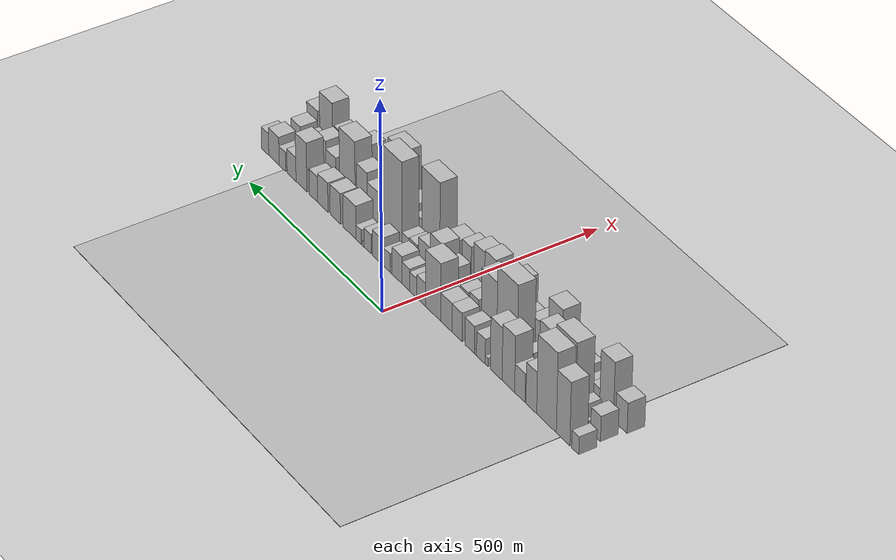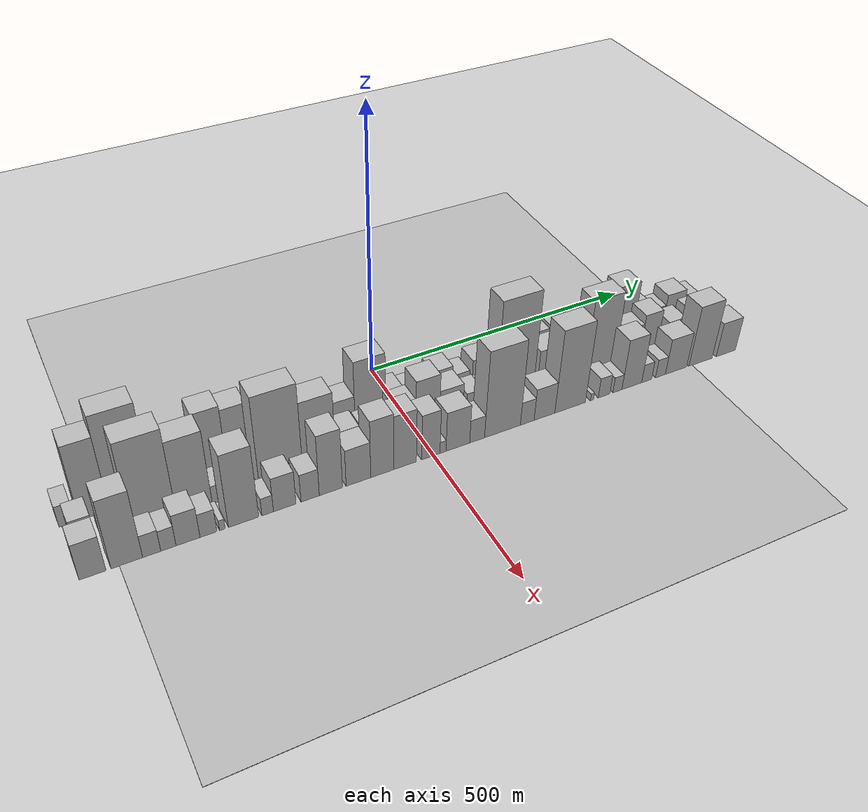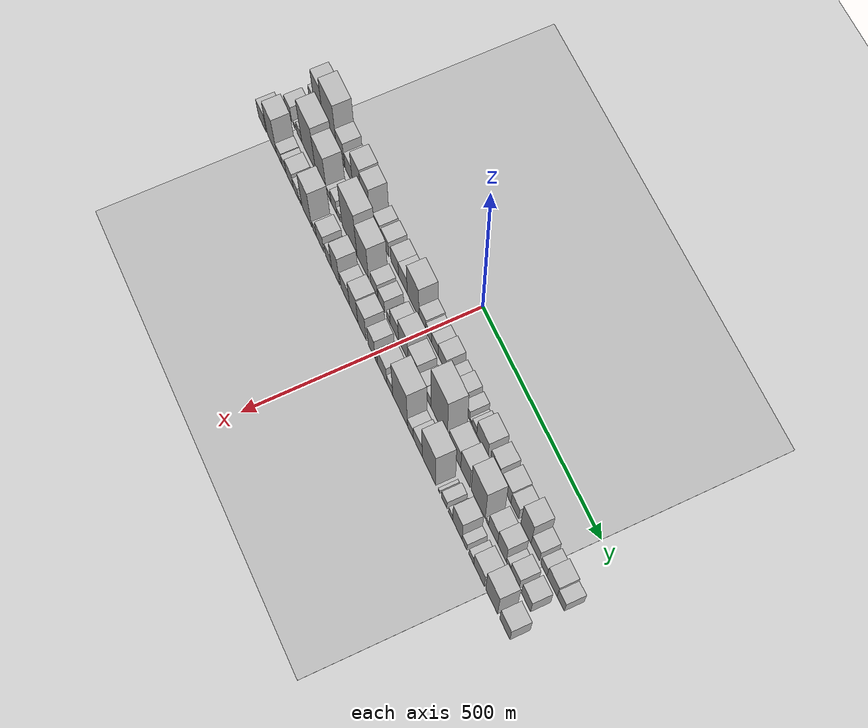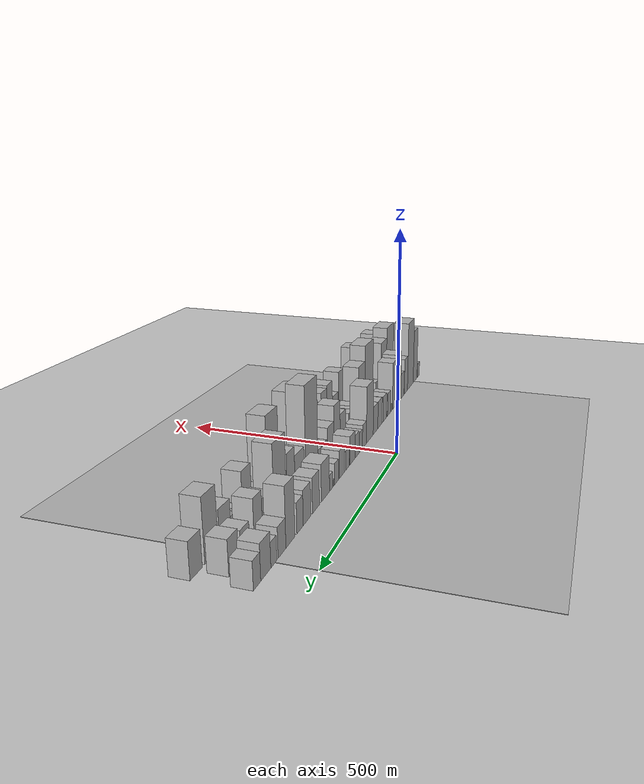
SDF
<?xml version="1.0" encoding="utf-8"?>

<sdf version="1.6">

   <world name="default">

      <gui fullscreen="0">

         <camera name="user_camera">

            <pose>-15 0 4.57585 0 0 0</pose>

            <view_controller>orbit</view_controller>

         </camera>

      </gui>

      <scene>

         <sky>

           <clouds>

             <speed>12</speed>

           </clouds>

         </sky>

         <ambient>0.4 0.4 0.4 1</ambient>

         <background>0.7 0.7 0.7 1</background>

         <shadows>1</shadows>

      </scene>

      <gravity>0 0 -9.8066</gravity>

      <magnetic_field>6e-06 2.3e-05 -4.2e-05</magnetic_field>

      <physics default="0" name="default_physics" type="ode">

         <ode>

            <solver>

               <type>quick</type>

               <iters>10</iters>

               <sor>1.0</sor>

               <use_dynamic_moi_rescaling>0</use_dynamic_moi_rescaling>

            </solver>

            <constraints>

               <cfm>0</cfm>

               <erp>0.2</erp>

               <contact_max_correcting_vel>100</contact_max_correcting_vel>

               <contact_surface_layer>0.001</contact_surface_layer>

            </constraints>

         </ode>

         <max_step_size>0.004</max_step_size>

         <real_time_factor>1</real_time_factor>

         <real_time_update_rate>250</real_time_update_rate>

      </physics>

      <light name="sun" type="directional">

         <cast_shadows>1</cast_shadows>

         <pose>0 0 10 0 0 0</pose>

         <diffuse>0.8 0.8 0.8 1</diffuse>

         <specular>0.2 0.2 0.2 1</specular>

         <attenuation>

            <range>1000</range>

            <constant>0.9</constant>

            <linear>0.01</linear>

            <quadratic>0.001</quadratic>

         </attenuation>

         <direction>-0.5 0.1 -0.9</direction>

      </light>

      <include>

         <name>ground_plane_1</name>

         <uri>model://HANNAS_ground_plane</uri>

         <pose>0 0 0  0 0 0</pose>

      </include>

      <include>

         <name>ground_plane_2</name>

         <uri>model://HANNAS_ground_plane</uri>

         <pose>100 0 0  0 0 0</pose>

      </include>

      <model name="building_1">

         <static>1</static>

         <pose frame="">100.0000 -548.1899 0 0.000000 0.000000 0.000000</pose>

         <link name="link">

            <pose frame="">0 0 21.00 0 0 0</pose>

            <collision name="collision">

               <geometry>

                  <box>

                     <size>40.0000 23.6201 42.0000</size>

                  </box>

               </geometry>

               <max_contacts>10</max_contacts>

               <surface>

                  <contact>

                     <ode/>

                  </contact>

                  <bounce/>

                  <friction>

                     <torsional>

                        <ode/>

                     </torsional>

                     <ode/>

                  </friction>

               </surface>

            </collision>

            <visual name="visual">

               <cast_shadows>0</cast_shadows>

               <geometry>

                  <box>

                     <size>40.0000 23.6201 42.0000</size>

                  </box>

               </geometry>

               <material>

                  <script>

                     <uri>model://HANNAS_wall/materials/scripts</uri>

                     <uri>model://HANNAS_wall/materials/textures</uri>

                     <name>vrc/HANNAS_wall</name>

                  </script>

               </material>

            </visual>

            <self_collide>0</self_collide>

            <enable_wind>0</enable_wind>

            <kinematic>0</kinematic>

         </link>

      </model>

      <model name="building_2">

         <static>1</static>

         <pose frame="">100.0000 -507.7143 0 0.000000 0.000000 0.000000</pose>

         <link name="link">

            <pose frame="">0 0 75.00 0 0 0</pose>

            <collision name="collision">

               <geometry>

                  <box>

                     <size>40.0000 45.3312 150.0000</size>

                  </box>

               </geometry>

               <max_contacts>10</max_contacts>

               <surface>

                  <contact>

                     <ode/>

                  </contact>

                  <bounce/>

                  <friction>

                     <torsional>

                        <ode/>

                     </torsional>

                     <ode/>

                  </friction>

               </surface>

            </collision>

            <visual name="visual">

               <cast_shadows>0</cast_shadows>

               <geometry>

                  <box>

                     <size>40.0000 45.3312 150.0000</size>

                  </box>

               </geometry>

               <material>

                  <script>

                     <uri>model://HANNAS_wall/materials/scripts</uri>

                     <uri>model://HANNAS_wall/materials/textures</uri>

                     <name>vrc/HANNAS_wall</name>

                  </script>

               </material>

            </visual>

            <self_collide>0</self_collide>

            <enable_wind>0</enable_wind>

            <kinematic>0</kinematic>

         </link>

      </model>

      <model name="building_3">

         <static>1</static>

         <pose frame="">100.0000 -451.9256 0 0.000000 0.000000 0.000000</pose>

         <link name="link">

            <pose frame="">0 0 94.50 0 0 0</pose>

            <collision name="collision">

               <geometry>

                  <box>

                     <size>40.0000 66.2461 189.0000</size>

                  </box>

               </geometry>

               <max_contacts>10</max_contacts>

               <surface>

                  <contact>

                     <ode/>

                  </contact>

                  <bounce/>

                  <friction>

                     <torsional>

                        <ode/>

                     </torsional>

                     <ode/>

                  </friction>

               </surface>

            </collision>

            <visual name="visual">

               <cast_shadows>0</cast_shadows>

               <geometry>

                  <box>

                     <size>40.0000 66.2461 189.0000</size>

                  </box>

               </geometry>

               <material>

                  <script>

                     <uri>model://HANNAS_wall/materials/scripts</uri>

                     <uri>model://HANNAS_wall/materials/textures</uri>

                     <name>vrc/HANNAS_wall</name>

                  </script>

               </material>

            </visual>

            <self_collide>0</self_collide>

            <enable_wind>0</enable_wind>

            <kinematic>0</kinematic>

         </link>

      </model>

      <model name="building_4">

         <static>1</static>

         <pose frame="">100.0000 -400.5581 0 0.000000 0.000000 0.000000</pose>

         <link name="link">

            <pose frame="">0 0 49.50 0 0 0</pose>

            <collision name="collision">

               <geometry>

                  <box>

                     <size>40.0000 36.4890 99.0000</size>

                  </box>

               </geometry>

               <max_contacts>10</max_contacts>

               <surface>

                  <contact>

                     <ode/>

                  </contact>

                  <bounce/>

                  <friction>

                     <torsional>

                        <ode/>

                     </torsional>

                     <ode/>

                  </friction>

               </surface>

            </collision>

            <visual name="visual">

               <cast_shadows>0</cast_shadows>

               <geometry>

                  <box>

                     <size>40.0000 36.4890 99.0000</size>

                  </box>

               </geometry>

               <material>

                  <script>

                     <uri>model://HANNAS_wall/materials/scripts</uri>

                     <uri>model://HANNAS_wall/materials/textures</uri>

                     <name>vrc/HANNAS_wall</name>

                  </script>

               </material>

            </visual>

            <self_collide>0</self_collide>

            <enable_wind>0</enable_wind>

            <kinematic>0</kinematic>

         </link>

      </model>

      <model name="building_5">

         <static>1</static>

         <pose frame="">100.0000 -361.6090 0 0.000000 0.000000 0.000000</pose>

         <link name="link">

            <pose frame="">0 0 34.50 0 0 0</pose>

            <collision name="collision">

               <geometry>

                  <box>

                     <size>40.0000 35.4092 69.0000</size>

                  </box>

               </geometry>

               <max_contacts>10</max_contacts>

               <surface>

                  <contact>

                     <ode/>

                  </contact>

                  <bounce/>

                  <friction>

                     <torsional>

                        <ode/>

                     </torsional>

                     <ode/>

                  </friction>

               </surface>

            </collision>

            <visual name="visual">

               <cast_shadows>0</cast_shadows>

               <geometry>

                  <box>

                     <size>40.0000 35.4092 69.0000</size>

                  </box>

               </geometry>

               <material>

                  <script>

                     <uri>model://HANNAS_wall/materials/scripts</uri>

                     <uri>model://HANNAS_wall/materials/textures</uri>

                     <name>vrc/HANNAS_wall</name>

                  </script>

               </material>

            </visual>

            <self_collide>0</self_collide>

            <enable_wind>0</enable_wind>

            <kinematic>0</kinematic>

         </link>

      </model>

      <model name="building_6">

         <static>1</static>

         <pose frame="">100.0000 -322.3359 0 0.000000 0.000000 0.000000</pose>

         <link name="link">

            <pose frame="">0 0 67.50 0 0 0</pose>

            <collision name="collision">

               <geometry>

                  <box>

                     <size>40.0000 43.1370 135.0000</size>

                  </box>

               </geometry>

               <max_contacts>10</max_contacts>

               <surface>

                  <contact>

                     <ode/>

                  </contact>

                  <bounce/>

                  <friction>

                     <torsional>

                        <ode/>

                     </torsional>

                     <ode/>

                  </friction>

               </surface>

            </collision>

            <visual name="visual">

               <cast_shadows>0</cast_shadows>

               <geometry>

                  <box>

                     <size>40.0000 43.1370 135.0000</size>

                  </box>

               </geometry>

               <material>

                  <script>

                     <uri>model://HANNAS_wall/materials/scripts</uri>

                     <uri>model://HANNAS_wall/materials/textures</uri>

                     <name>vrc/HANNAS_wall</name>

                  </script>

               </material>

            </visual>

            <self_collide>0</self_collide>

            <enable_wind>0</enable_wind>

            <kinematic>0</kinematic>

         </link>

      </model>

      <model name="building_7">

         <static>1</static>

         <pose frame="">100.0000 -280.2449 0 0.000000 0.000000 0.000000</pose>

         <link name="link">

            <pose frame="">0 0 63.00 0 0 0</pose>

            <collision name="collision">

               <geometry>

                  <box>

                     <size>40.0000 41.0449 126.0000</size>

                  </box>

               </geometry>

               <max_contacts>10</max_contacts>

               <surface>

                  <contact>

                     <ode/>

                  </contact>

                  <bounce/>

                  <friction>

                     <torsional>

                        <ode/>

                     </torsional>

                     <ode/>

                  </friction>

               </surface>

            </collision>

            <visual name="visual">

               <cast_shadows>0</cast_shadows>

               <geometry>

                  <box>

                     <size>40.0000 41.0449 126.0000</size>

                  </box>

               </geometry>

               <material>

                  <script>

                     <uri>model://HANNAS_wall/materials/scripts</uri>

                     <uri>model://HANNAS_wall/materials/textures</uri>

                     <name>vrc/HANNAS_wall</name>

                  </script>

               </material>

            </visual>

            <self_collide>0</self_collide>

            <enable_wind>0</enable_wind>

            <kinematic>0</kinematic>

         </link>

      </model>

      <model name="building_8">

         <static>1</static>

         <pose frame="">100.0000 -246.9305 0 0.000000 0.000000 0.000000</pose>

         <link name="link">

            <pose frame="">0 0 10.50 0 0 0</pose>

            <collision name="collision">

               <geometry>

                  <box>

                     <size>40.0000 9.5841 21.0000</size>

                  </box>

               </geometry>

               <max_contacts>10</max_contacts>

               <surface>

                  <contact>

                     <ode/>

                  </contact>

                  <bounce/>

                  <friction>

                     <torsional>

                        <ode/>

                     </torsional>

                     <ode/>

                  </friction>

               </surface>

            </collision>

            <visual name="visual">

               <cast_shadows>0</cast_shadows>

               <geometry>

                  <box>

                     <size>40.0000 9.5841 21.0000</size>

                  </box>

               </geometry>

               <material>

                  <script>

                     <uri>model://HANNAS_wall/materials/scripts</uri>

                     <uri>model://HANNAS_wall/materials/textures</uri>

                     <name>vrc/HANNAS_wall</name>

                  </script>

               </material>

            </visual>

            <self_collide>0</self_collide>

            <enable_wind>0</enable_wind>

            <kinematic>0</kinematic>

         </link>

      </model>

      <model name="building_9">

         <static>1</static>

         <pose frame="">100.0000 -226.8471 0 0.000000 0.000000 0.000000</pose>

         <link name="link">

            <pose frame="">0 0 30.00 0 0 0</pose>

            <collision name="collision">

               <geometry>

                  <box>

                     <size>40.0000 30.5827 60.0000</size>

                  </box>

               </geometry>

               <max_contacts>10</max_contacts>

               <surface>

                  <contact>

                     <ode/>

                  </contact>

                  <bounce/>

                  <friction>

                     <torsional>

                        <ode/>

                     </torsional>

                     <ode/>

                  </friction>

               </surface>

            </collision>

            <visual name="visual">

               <cast_shadows>0</cast_shadows>

               <geometry>

                  <box>

                     <size>40.0000 30.5827 60.0000</size>

                  </box>

               </geometry>

               <material>

                  <script>

                     <uri>model://HANNAS_wall/materials/scripts</uri>

                     <uri>model://HANNAS_wall/materials/textures</uri>

                     <name>vrc/HANNAS_wall</name>

                  </script>

               </material>

            </visual>

            <self_collide>0</self_collide>

            <enable_wind>0</enable_wind>

            <kinematic>0</kinematic>

         </link>

      </model>

      <model name="building_10">

         <static>1</static>

         <pose frame="">100.0000 -207.9256 0 0.000000 0.000000 0.000000</pose>

         <link name="link">

            <pose frame="">0 0 7.50 0 0 0</pose>

            <collision name="collision">

               <geometry>

                  <box>

                     <size>40.0000 7.2604 15.0000</size>

                  </box>

               </geometry>

               <max_contacts>10</max_contacts>

               <surface>

                  <contact>

                     <ode/>

                  </contact>

                  <bounce/>

                  <friction>

                     <torsional>

                        <ode/>

                     </torsional>

                     <ode/>

                  </friction>

               </surface>

            </collision>

            <visual name="visual">

               <cast_shadows>0</cast_shadows>

               <geometry>

                  <box>

                     <size>40.0000 7.2604 15.0000</size>

                  </box>

               </geometry>

               <material>

                  <script>

                     <uri>model://HANNAS_wall/materials/scripts</uri>

                     <uri>model://HANNAS_wall/materials/textures</uri>

                     <name>vrc/HANNAS_wall</name>

                  </script>

               </material>

            </visual>

            <self_collide>0</self_collide>

            <enable_wind>0</enable_wind>

            <kinematic>0</kinematic>

         </link>

      </model>

      <model name="building_11">

         <static>1</static>

         <pose frame="">100.0000 -187.4058 0 0.000000 0.000000 0.000000</pose>

         <link name="link">

            <pose frame="">0 0 33.00 0 0 0</pose>

            <collision name="collision">

               <geometry>

                  <box>

                     <size>40.0000 33.7791 66.0000</size>

                  </box>

               </geometry>

               <max_contacts>10</max_contacts>

               <surface>

                  <contact>

                     <ode/>

                  </contact>

                  <bounce/>

                  <friction>

                     <torsional>

                        <ode/>

                     </torsional>

                     <ode/>

                  </friction>

               </surface>

            </collision>

            <visual name="visual">

               <cast_shadows>0</cast_shadows>

               <geometry>

                  <box>

                     <size>40.0000 33.7791 66.0000</size>

                  </box>

               </geometry>

               <material>

                  <script>

                     <uri>model://HANNAS_wall/materials/scripts</uri>

                     <uri>model://HANNAS_wall/materials/textures</uri>

                     <name>vrc/HANNAS_wall</name>

                  </script>

               </material>

            </visual>

            <self_collide>0</self_collide>

            <enable_wind>0</enable_wind>

            <kinematic>0</kinematic>

         </link>

      </model>

      <model name="building_12">

         <static>1</static>

         <pose frame="">100.0000 -142.6966 0 0.000000 0.000000 0.000000</pose>

         <link name="link">

            <pose frame="">0 0 34.50 0 0 0</pose>

            <collision name="collision">

               <geometry>

                  <box>

                     <size>40.0000 35.6393 69.0000</size>

                  </box>

               </geometry>

               <max_contacts>10</max_contacts>

               <surface>

                  <contact>

                     <ode/>

                  </contact>

                  <bounce/>

                  <friction>

                     <torsional>

                        <ode/>

                     </torsional>

                     <ode/>

                  </friction>

               </surface>

            </collision>

            <visual name="visual">

               <cast_shadows>0</cast_shadows>

               <geometry>

                  <box>

                     <size>40.0000 35.6393 69.0000</size>

                  </box>

               </geometry>

               <material>

                  <script>

                     <uri>model://HANNAS_wall/materials/scripts</uri>

                     <uri>model://HANNAS_wall/materials/textures</uri>

                     <name>vrc/HANNAS_wall</name>

                  </script>

               </material>

            </visual>

            <self_collide>0</self_collide>

            <enable_wind>0</enable_wind>

            <kinematic>0</kinematic>

         </link>

      </model>

      <model name="building_13">

         <static>1</static>

         <pose frame="">100.0000 -105.0004 0 0.000000 0.000000 0.000000</pose>

         <link name="link">

            <pose frame="">0 0 34.50 0 0 0</pose>

            <collision name="collision">

               <geometry>

                  <box>

                     <size>40.0000 39.7530 69.0000</size>

                  </box>

               </geometry>

               <max_contacts>10</max_contacts>

               <surface>

                  <contact>

                     <ode/>

                  </contact>

                  <bounce/>

                  <friction>

                     <torsional>

                        <ode/>

                     </torsional>

                     <ode/>

                  </friction>

               </surface>

            </collision>

            <visual name="visual">

               <cast_shadows>0</cast_shadows>

               <geometry>

                  <box>

                     <size>40.0000 39.7530 69.0000</size>

                  </box>

               </geometry>

               <material>

                  <script>

                     <uri>model://HANNAS_wall/materials/scripts</uri>

                     <uri>model://HANNAS_wall/materials/textures</uri>

                     <name>vrc/HANNAS_wall</name>

                  </script>

               </material>

            </visual>

            <self_collide>0</self_collide>

            <enable_wind>0</enable_wind>

            <kinematic>0</kinematic>

         </link>

      </model>

      <model name="building_14">

         <static>1</static>

         <pose frame="">100.0000 -58.0740 0 0.000000 0.000000 0.000000</pose>

         <link name="link">

            <pose frame="">0 0 69.00 0 0 0</pose>

            <collision name="collision">

               <geometry>

                  <box>

                     <size>40.0000 54.0998 138.0000</size>

                  </box>

               </geometry>

               <max_contacts>10</max_contacts>

               <surface>

                  <contact>

                     <ode/>

                  </contact>

                  <bounce/>

                  <friction>

                     <torsional>

                        <ode/>

                     </torsional>

                     <ode/>

                  </friction>

               </surface>

            </collision>

            <visual name="visual">

               <cast_shadows>0</cast_shadows>

               <geometry>

                  <box>

                     <size>40.0000 54.0998 138.0000</size>

                  </box>

               </geometry>

               <material>

                  <script>

                     <uri>model://HANNAS_wall/materials/scripts</uri>

                     <uri>model://HANNAS_wall/materials/textures</uri>

                     <name>vrc/HANNAS_wall</name>

                  </script>

               </material>

            </visual>

            <self_collide>0</self_collide>

            <enable_wind>0</enable_wind>

            <kinematic>0</kinematic>

         </link>

      </model>

      <model name="building_15">

         <static>1</static>

         <pose frame="">100.0000 -15.1862 0 0.000000 0.000000 0.000000</pose>

         <link name="link">

            <pose frame="">0 0 28.50 0 0 0</pose>

            <collision name="collision">

               <geometry>

                  <box>

                     <size>40.0000 31.6759 57.0000</size>

                  </box>

               </geometry>

               <max_contacts>10</max_contacts>

               <surface>

                  <contact>

                     <ode/>

                  </contact>

                  <bounce/>

                  <friction>

                     <torsional>

                        <ode/>

                     </torsional>

                     <ode/>

                  </friction>

               </surface>

            </collision>

            <visual name="visual">

               <cast_shadows>0</cast_shadows>

               <geometry>

                  <box>

                     <size>40.0000 31.6759 57.0000</size>

                  </box>

               </geometry>

               <material>

                  <script>

                     <uri>model://HANNAS_wall/materials/scripts</uri>

                     <uri>model://HANNAS_wall/materials/textures</uri>

                     <name>vrc/HANNAS_wall</name>

                  </script>

               </material>

            </visual>

            <self_collide>0</self_collide>

            <enable_wind>0</enable_wind>

            <kinematic>0</kinematic>

         </link>

      </model>

      <model name="building_16">

         <static>1</static>

         <pose frame="">100.0000 13.5166 0 0.000000 0.000000 0.000000</pose>

         <link name="link">

            <pose frame="">0 0 24.00 0 0 0</pose>

            <collision name="collision">

               <geometry>

                  <box>

                     <size>40.0000 25.7296 48.0000</size>

                  </box>

               </geometry>

               <max_contacts>10</max_contacts>

               <surface>

                  <contact>

                     <ode/>

                  </contact>

                  <bounce/>

                  <friction>

                     <torsional>

                        <ode/>

                     </torsional>

                     <ode/>

                  </friction>

               </surface>

            </collision>

            <visual name="visual">

               <cast_shadows>0</cast_shadows>

               <geometry>

                  <box>

                     <size>40.0000 25.7296 48.0000</size>

                  </box>

               </geometry>

               <material>

                  <script>

                     <uri>model://HANNAS_wall/materials/scripts</uri>

                     <uri>model://HANNAS_wall/materials/textures</uri>

                     <name>vrc/HANNAS_wall</name>

                  </script>

               </material>

            </visual>

            <self_collide>0</self_collide>

            <enable_wind>0</enable_wind>

            <kinematic>0</kinematic>

         </link>

      </model>

      <model name="building_17">

         <static>1</static>

         <pose frame="">100.0000 40.5990 0 0.000000 0.000000 0.000000</pose>

         <link name="link">

            <pose frame="">0 0 27.00 0 0 0</pose>

            <collision name="collision">

               <geometry>

                  <box>

                     <size>40.0000 28.4353 54.0000</size>

                  </box>

               </geometry>

               <max_contacts>10</max_contacts>

               <surface>

                  <contact>

                     <ode/>

                  </contact>

                  <bounce/>

                  <friction>

                     <torsional>

                        <ode/>

                     </torsional>

                     <ode/>

                  </friction>

               </surface>

            </collision>

            <visual name="visual">

               <cast_shadows>0</cast_shadows>

               <geometry>

                  <box>

                     <size>40.0000 28.4353 54.0000</size>

                  </box>

               </geometry>

               <material>

                  <script>

                     <uri>model://HANNAS_wall/materials/scripts</uri>

                     <uri>model://HANNAS_wall/materials/textures</uri>

                     <name>vrc/HANNAS_wall</name>

                  </script>

               </material>

            </visual>

            <self_collide>0</self_collide>

            <enable_wind>0</enable_wind>

            <kinematic>0</kinematic>

         </link>

      </model>

      <model name="building_18">

         <static>1</static>

         <pose frame="">100.0000 73.1236 0 0.000000 0.000000 0.000000</pose>

         <link name="link">

            <pose frame="">0 0 33.00 0 0 0</pose>

            <collision name="collision">

               <geometry>

                  <box>

                     <size>40.0000 36.6138 66.0000</size>

                  </box>

               </geometry>

               <max_contacts>10</max_contacts>

               <surface>

                  <contact>

                     <ode/>

                  </contact>

                  <bounce/>

                  <friction>

                     <torsional>

                        <ode/>

                     </torsional>

                     <ode/>

                  </friction>

               </surface>

            </collision>

            <visual name="visual">

               <cast_shadows>0</cast_shadows>

               <geometry>

                  <box>

                     <size>40.0000 36.6138 66.0000</size>

                  </box>

               </geometry>

               <material>

                  <script>

                     <uri>model://HANNAS_wall/materials/scripts</uri>

                     <uri>model://HANNAS_wall/materials/textures</uri>

                     <name>vrc/HANNAS_wall</name>

                  </script>

               </material>

            </visual>

            <self_collide>0</self_collide>

            <enable_wind>0</enable_wind>

            <kinematic>0</kinematic>

         </link>

      </model>

      <model name="building_19">

         <static>1</static>

         <pose frame="">100.0000 95.1760 0 0.000000 0.000000 0.000000</pose>

         <link name="link">

            <pose frame="">0 0 9.00 0 0 0</pose>

            <collision name="collision">

               <geometry>

                  <box>

                     <size>40.0000 7.4911 18.0000</size>

                  </box>

               </geometry>

               <max_contacts>10</max_contacts>

               <surface>

                  <contact>

                     <ode/>

                  </contact>

                  <bounce/>

                  <friction>

                     <torsional>

                        <ode/>

                     </torsional>

                     <ode/>

                  </friction>

               </surface>

            </collision>

            <visual name="visual">

               <cast_shadows>0</cast_shadows>

               <geometry>

                  <box>

                     <size>40.0000 7.4911 18.0000</size>

                  </box>

               </geometry>

               <material>

                  <script>

                     <uri>model://HANNAS_wall/materials/scripts</uri>

                     <uri>model://HANNAS_wall/materials/textures</uri>

                     <name>vrc/HANNAS_wall</name>

                  </script>

               </material>

            </visual>

            <self_collide>0</self_collide>

            <enable_wind>0</enable_wind>

            <kinematic>0</kinematic>

         </link>

      </model>

      <model name="building_20">

         <static>1</static>

         <pose frame="">100.0000 111.1331 0 0.000000 0.000000 0.000000</pose>

         <link name="link">

            <pose frame="">0 0 22.50 0 0 0</pose>

            <collision name="collision">

               <geometry>

                  <box>

                     <size>40.0000 24.4231 45.0000</size>

                  </box>

               </geometry>

               <max_contacts>10</max_contacts>

               <surface>

                  <contact>

                     <ode/>

                  </contact>

                  <bounce/>

                  <friction>

                     <torsional>

                        <ode/>

                     </torsional>

                     <ode/>

                  </friction>

               </surface>

            </collision>

            <visual name="visual">

               <cast_shadows>0</cast_shadows>

               <geometry>

                  <box>

                     <size>40.0000 24.4231 45.0000</size>

                  </box>

               </geometry>

               <material>

                  <script>

                     <uri>model://HANNAS_wall/materials/scripts</uri>

                     <uri>model://HANNAS_wall/materials/textures</uri>

                     <name>vrc/HANNAS_wall</name>

                  </script>

               </material>

            </visual>

            <self_collide>0</self_collide>

            <enable_wind>0</enable_wind>

            <kinematic>0</kinematic>

         </link>

      </model>

      <model name="building_21">

         <static>1</static>

         <pose frame="">100.0000 146.0212 0 0.000000 0.000000 0.000000</pose>

         <link name="link">

            <pose frame="">0 0 31.50 0 0 0</pose>

            <collision name="collision">

               <geometry>

                  <box>

                     <size>40.0000 35.3532 63.0000</size>

                  </box>

               </geometry>

               <max_contacts>10</max_contacts>

               <surface>

                  <contact>

                     <ode/>

                  </contact>

                  <bounce/>

                  <friction>

                     <torsional>

                        <ode/>

                     </torsional>

                     <ode/>

                  </friction>

               </surface>

            </collision>

            <visual name="visual">

               <cast_shadows>0</cast_shadows>

               <geometry>

                  <box>

                     <size>40.0000 35.3532 63.0000</size>

                  </box>

               </geometry>

               <material>

                  <script>

                     <uri>model://HANNAS_wall/materials/scripts</uri>

                     <uri>model://HANNAS_wall/materials/textures</uri>

                     <name>vrc/HANNAS_wall</name>

                  </script>

               </material>

            </visual>

            <self_collide>0</self_collide>

            <enable_wind>0</enable_wind>

            <kinematic>0</kinematic>

         </link>

      </model>

      <model name="building_22">

         <static>1</static>

         <pose frame="">100.0000 181.5563 0 0.000000 0.000000 0.000000</pose>

         <link name="link">

            <pose frame="">0 0 24.00 0 0 0</pose>

            <collision name="collision">

               <geometry>

                  <box>

                     <size>40.0000 25.7168 48.0000</size>

                  </box>

               </geometry>

               <max_contacts>10</max_contacts>

               <surface>

                  <contact>

                     <ode/>

                  </contact>

                  <bounce/>

                  <friction>

                     <torsional>

                        <ode/>

                     </torsional>

                     <ode/>

                  </friction>

               </surface>

            </collision>

            <visual name="visual">

               <cast_shadows>0</cast_shadows>

               <geometry>

                  <box>

                     <size>40.0000 25.7168 48.0000</size>

                  </box>

               </geometry>

               <material>

                  <script>

                     <uri>model://HANNAS_wall/materials/scripts</uri>

                     <uri>model://HANNAS_wall/materials/textures</uri>

                     <name>vrc/HANNAS_wall</name>

                  </script>

               </material>

            </visual>

            <self_collide>0</self_collide>

            <enable_wind>0</enable_wind>

            <kinematic>0</kinematic>

         </link>

      </model>

      <model name="building_23">

         <static>1</static>

         <pose frame="">100.0000 198.0065 0 0.000000 0.000000 0.000000</pose>

         <link name="link">

            <pose frame="">0 0 7.50 0 0 0</pose>

            <collision name="collision">

               <geometry>

                  <box>

                     <size>40.0000 7.1837 15.0000</size>

                  </box>

               </geometry>

               <max_contacts>10</max_contacts>

               <surface>

                  <contact>

                     <ode/>

                  </contact>

                  <bounce/>

                  <friction>

                     <torsional>

                        <ode/>

                     </torsional>

                     <ode/>

                  </friction>

               </surface>

            </collision>

            <visual name="visual">

               <cast_shadows>0</cast_shadows>

               <geometry>

                  <box>

                     <size>40.0000 7.1837 15.0000</size>

                  </box>

               </geometry>

               <material>

                  <script>

                     <uri>model://HANNAS_wall/materials/scripts</uri>

                     <uri>model://HANNAS_wall/materials/textures</uri>

                     <name>vrc/HANNAS_wall</name>

                  </script>

               </material>

            </visual>

            <self_collide>0</self_collide>

            <enable_wind>0</enable_wind>

            <kinematic>0</kinematic>

         </link>

      </model>

      <model name="building_24">

         <static>1</static>

         <pose frame="">100.0000 214.8388 0 0.000000 0.000000 0.000000</pose>

         <link name="link">

            <pose frame="">0 0 18.00 0 0 0</pose>

            <collision name="collision">

               <geometry>

                  <box>

                     <size>40.0000 20.4810 36.0000</size>

                  </box>

               </geometry>

               <max_contacts>10</max_contacts>

               <surface>

                  <contact>

                     <ode/>

                  </contact>

                  <bounce/>

                  <friction>

                     <torsional>

                        <ode/>

                     </torsional>

                     <ode/>

                  </friction>

               </surface>

            </collision>

            <visual name="visual">

               <cast_shadows>0</cast_shadows>

               <geometry>

                  <box>

                     <size>40.0000 20.4810 36.0000</size>

                  </box>

               </geometry>

               <material>

                  <script>

                     <uri>model://HANNAS_wall/materials/scripts</uri>

                     <uri>model://HANNAS_wall/materials/textures</uri>

                     <name>vrc/HANNAS_wall</name>

                  </script>

               </material>

            </visual>

            <self_collide>0</self_collide>

            <enable_wind>0</enable_wind>

            <kinematic>0</kinematic>

         </link>

      </model>

      <model name="building_25">

         <static>1</static>

         <pose frame="">100.0000 249.1997 0 0.000000 0.000000 0.000000</pose>

         <link name="link">

            <pose frame="">0 0 40.50 0 0 0</pose>

            <collision name="collision">

               <geometry>

                  <box>

                     <size>40.0000 48.2407 81.0000</size>

                  </box>

               </geometry>

               <max_contacts>10</max_contacts>

               <surface>

                  <contact>

                     <ode/>

                  </contact>

                  <bounce/>

                  <friction>

                     <torsional>

                        <ode/>

                     </torsional>

                     <ode/>

                  </friction>

               </surface>

            </collision>

            <visual name="visual">

               <cast_shadows>0</cast_shadows>

               <geometry>

                  <box>

                     <size>40.0000 48.2407 81.0000</size>

                  </box>

               </geometry>

               <material>

                  <script>

                     <uri>model://HANNAS_wall/materials/scripts</uri>

                     <uri>model://HANNAS_wall/materials/textures</uri>

                     <name>vrc/HANNAS_wall</name>

                  </script>

               </material>

            </visual>

            <self_collide>0</self_collide>

            <enable_wind>0</enable_wind>

            <kinematic>0</kinematic>

         </link>

      </model>

      <model name="building_26">

         <static>1</static>

         <pose frame="">100.0000 302.8571 0 0.000000 0.000000 0.000000</pose>

         <link name="link">

            <pose frame="">0 0 37.50 0 0 0</pose>

            <collision name="collision">

               <geometry>

                  <box>

                     <size>40.0000 39.0741 75.0000</size>

                  </box>

               </geometry>

               <max_contacts>10</max_contacts>

               <surface>

                  <contact>

                     <ode/>

                  </contact>

                  <bounce/>

                  <friction>

                     <torsional>

                        <ode/>

                     </torsional>

                     <ode/>

                  </friction>

               </surface>

            </collision>

            <visual name="visual">

               <cast_shadows>0</cast_shadows>

               <geometry>

                  <box>

                     <size>40.0000 39.0741 75.0000</size>

                  </box>

               </geometry>

               <material>

                  <script>

                     <uri>model://HANNAS_wall/materials/scripts</uri>

                     <uri>model://HANNAS_wall/materials/textures</uri>

                     <name>vrc/HANNAS_wall</name>

                  </script>

               </material>

            </visual>

            <self_collide>0</self_collide>

            <enable_wind>0</enable_wind>

            <kinematic>0</kinematic>

         </link>

      </model>

      <model name="building_27">

         <static>1</static>

         <pose frame="">100.0000 350.1309 0 0.000000 0.000000 0.000000</pose>

         <link name="link">

            <pose frame="">0 0 36.00 0 0 0</pose>

            <collision name="collision">

               <geometry>

                  <box>

                     <size>40.0000 39.4736 72.0000</size>

                  </box>

               </geometry>

               <max_contacts>10</max_contacts>

               <surface>

                  <contact>

                     <ode/>

                  </contact>

                  <bounce/>

                  <friction>

                     <torsional>

                        <ode/>

                     </torsional>

                     <ode/>

                  </friction>

               </surface>

            </collision>

            <visual name="visual">

               <cast_shadows>0</cast_shadows>

               <geometry>

                  <box>

                     <size>40.0000 39.4736 72.0000</size>

                  </box>

               </geometry>

               <material>

                  <script>

                     <uri>model://HANNAS_wall/materials/scripts</uri>

                     <uri>model://HANNAS_wall/materials/textures</uri>

                     <name>vrc/HANNAS_wall</name>

                  </script>

               </material>

            </visual>

            <self_collide>0</self_collide>

            <enable_wind>0</enable_wind>

            <kinematic>0</kinematic>

         </link>

      </model>

      <model name="building_28">

         <static>1</static>

         <pose frame="">100.0000 385.9384 0 0.000000 0.000000 0.000000</pose>

         <link name="link">

            <pose frame="">0 0 31.50 0 0 0</pose>

            <collision name="collision">

               <geometry>

                  <box>

                     <size>40.0000 32.1412 63.0000</size>

                  </box>

               </geometry>

               <max_contacts>10</max_contacts>

               <surface>

                  <contact>

                     <ode/>

                  </contact>

                  <bounce/>

                  <friction>

                     <torsional>

                        <ode/>

                     </torsional>

                     <ode/>

                  </friction>

               </surface>

            </collision>

            <visual name="visual">

               <cast_shadows>0</cast_shadows>

               <geometry>

                  <box>

                     <size>40.0000 32.1412 63.0000</size>

                  </box>

               </geometry>

               <material>

                  <script>

                     <uri>model://HANNAS_wall/materials/scripts</uri>

                     <uri>model://HANNAS_wall/materials/textures</uri>

                     <name>vrc/HANNAS_wall</name>

                  </script>

               </material>

            </visual>

            <self_collide>0</self_collide>

            <enable_wind>0</enable_wind>

            <kinematic>0</kinematic>

         </link>

      </model>

      <model name="building_29">

         <static>1</static>

         <pose frame="">100.0000 432.0686 0 0.000000 0.000000 0.000000</pose>

         <link name="link">

            <pose frame="">0 0 60.00 0 0 0</pose>

            <collision name="collision">

               <geometry>

                  <box>

                     <size>40.0000 42.1192 120.0000</size>

                  </box>

               </geometry>

               <max_contacts>10</max_contacts>

               <surface>

                  <contact>

                     <ode/>

                  </contact>

                  <bounce/>

                  <friction>

                     <torsional>

                        <ode/>

                     </torsional>

                     <ode/>

                  </friction>

               </surface>

            </collision>

            <visual name="visual">

               <cast_shadows>0</cast_shadows>

               <geometry>

                  <box>

                     <size>40.0000 42.1192 120.0000</size>

                  </box>

               </geometry>

               <material>

                  <script>

                     <uri>model://HANNAS_wall/materials/scripts</uri>

                     <uri>model://HANNAS_wall/materials/textures</uri>

                     <name>vrc/HANNAS_wall</name>

                  </script>

               </material>

            </visual>

            <self_collide>0</self_collide>

            <enable_wind>0</enable_wind>

            <kinematic>0</kinematic>

         </link>

      </model>

      <model name="building_30">

         <static>1</static>

         <pose frame="">100.0000 470.4809 0 0.000000 0.000000 0.000000</pose>

         <link name="link">

            <pose frame="">0 0 30.00 0 0 0</pose>

            <collision name="collision">

               <geometry>

                  <box>

                     <size>40.0000 34.7054 60.0000</size>

                  </box>

               </geometry>

               <max_contacts>10</max_contacts>

               <surface>

                  <contact>

                     <ode/>

                  </contact>

                  <bounce/>

                  <friction>

                     <torsional>

                        <ode/>

                     </torsional>

                     <ode/>

                  </friction>

               </surface>

            </collision>

            <visual name="visual">

               <cast_shadows>0</cast_shadows>

               <geometry>

                  <box>

                     <size>40.0000 34.7054 60.0000</size>

                  </box>

               </geometry>

               <material>

                  <script>

                     <uri>model://HANNAS_wall/materials/scripts</uri>

                     <uri>model://HANNAS_wall/materials/textures</uri>

                     <name>vrc/HANNAS_wall</name>

                  </script>

               </material>

            </visual>

            <self_collide>0</self_collide>

            <enable_wind>0</enable_wind>

            <kinematic>0</kinematic>

         </link>

      </model>

      <model name="building_31">

         <static>1</static>

         <pose frame="">100.0000 505.7154 0 0.000000 0.000000 0.000000</pose>

         <link name="link">

            <pose frame="">0 0 24.00 0 0 0</pose>

            <collision name="collision">

               <geometry>

                  <box>

                     <size>40.0000 25.7636 48.0000</size>

                  </box>

               </geometry>

               <max_contacts>10</max_contacts>

               <surface>

                  <contact>

                     <ode/>

                  </contact>

                  <bounce/>

                  <friction>

                     <torsional>

                        <ode/>

                     </torsional>

                     <ode/>

                  </friction>

               </surface>

            </collision>

            <visual name="visual">

               <cast_shadows>0</cast_shadows>

               <geometry>

                  <box>

                     <size>40.0000 25.7636 48.0000</size>

                  </box>

               </geometry>

               <material>

                  <script>

                     <uri>model://HANNAS_wall/materials/scripts</uri>

                     <uri>model://HANNAS_wall/materials/textures</uri>

                     <name>vrc/HANNAS_wall</name>

                  </script>

               </material>

            </visual>

            <self_collide>0</self_collide>

            <enable_wind>0</enable_wind>

            <kinematic>0</kinematic>

         </link>

      </model>

      <model name="building_32">

         <static>1</static>

         <pose frame="">100.0000 539.0281 0 0.000000 0.000000 0.000000</pose>

         <link name="link">

            <pose frame="">0 0 34.50 0 0 0</pose>

            <collision name="collision">

               <geometry>

                  <box>

                     <size>40.0000 40.8618 69.0000</size>

                  </box>

               </geometry>

               <max_contacts>10</max_contacts>

               <surface>

                  <contact>

                     <ode/>

                  </contact>

                  <bounce/>

                  <friction>

                     <torsional>

                        <ode/>

                     </torsional>

                     <ode/>

                  </friction>

               </surface>

            </collision>

            <visual name="visual">

               <cast_shadows>0</cast_shadows>

               <geometry>

                  <box>

                     <size>40.0000 40.8618 69.0000</size>

                  </box>

               </geometry>

               <material>

                  <script>

                     <uri>model://HANNAS_wall/materials/scripts</uri>

                     <uri>model://HANNAS_wall/materials/textures</uri>

                     <name>vrc/HANNAS_wall</name>

                  </script>

               </material>

            </visual>

            <self_collide>0</self_collide>

            <enable_wind>0</enable_wind>

            <kinematic>0</kinematic>

         </link>

      </model>

      <model name="building_33">

         <static>1</static>

         <pose frame="">100.0000 573.7321 0 0.000000 0.000000 0.000000</pose>

         <link name="link">

            <pose frame="">0 0 27.00 0 0 0</pose>

            <collision name="collision">

               <geometry>

                  <box>

                     <size>40.0000 28.5462 54.0000</size>

                  </box>

               </geometry>

               <max_contacts>10</max_contacts>

               <surface>

                  <contact>

                     <ode/>

                  </contact>

                  <bounce/>

                  <friction>

                     <torsional>

                        <ode/>

                     </torsional>

                     <ode/>

                  </friction>

               </surface>

            </collision>

            <visual name="visual">

               <cast_shadows>0</cast_shadows>

               <geometry>

                  <box>

                     <size>40.0000 28.5462 54.0000</size>

                  </box>

               </geometry>

               <material>

                  <script>

                     <uri>model://HANNAS_wall/materials/scripts</uri>

                     <uri>model://HANNAS_wall/materials/textures</uri>

                     <name>vrc/HANNAS_wall</name>

                  </script>

               </material>

            </visual>

            <self_collide>0</self_collide>

            <enable_wind>0</enable_wind>

            <kinematic>0</kinematic>

         </link>

      </model>

      <model name="building_34">

         <static>1</static>

         <pose frame="">155.0000 -533.9332 0 0.000000 0.000000 0.000000</pose>

         <link name="link">

            <pose frame="">0 0 30.00 0 0 0</pose>

            <collision name="collision">

               <geometry>

                  <box>

                     <size>40.0000 32.1335 60.0000</size>

                  </box>

               </geometry>

               <max_contacts>10</max_contacts>

               <surface>

                  <contact>

                     <ode/>

                  </contact>

                  <bounce/>

                  <friction>

                     <torsional>

                        <ode/>

                     </torsional>

                     <ode/>

                  </friction>

               </surface>

            </collision>

            <visual name="visual">

               <cast_shadows>0</cast_shadows>

               <geometry>

                  <box>

                     <size>40.0000 32.1335 60.0000</size>

                  </box>

               </geometry>

               <material>

                  <script>

                     <uri>model://HANNAS_wall/materials/scripts</uri>

                     <uri>model://HANNAS_wall/materials/textures</uri>

                     <name>vrc/HANNAS_wall</name>

                  </script>

               </material>

            </visual>

            <self_collide>0</self_collide>

            <enable_wind>0</enable_wind>

            <kinematic>0</kinematic>

         </link>

      </model>

      <model name="building_35">

         <static>1</static>

         <pose frame="">155.0000 -505.0855 0 0.000000 0.000000 0.000000</pose>

         <link name="link">

            <pose frame="">0 0 10.50 0 0 0</pose>

            <collision name="collision">

               <geometry>

                  <box>

                     <size>40.0000 9.5620 21.0000</size>

                  </box>

               </geometry>

               <max_contacts>10</max_contacts>

               <surface>

                  <contact>

                     <ode/>

                  </contact>

                  <bounce/>

                  <friction>

                     <torsional>

                        <ode/>

                     </torsional>

                     <ode/>

                  </friction>

               </surface>

            </collision>

            <visual name="visual">

               <cast_shadows>0</cast_shadows>

               <geometry>

                  <box>

                     <size>40.0000 9.5620 21.0000</size>

                  </box>

               </geometry>

               <material>

                  <script>

                     <uri>model://HANNAS_wall/materials/scripts</uri>

                     <uri>model://HANNAS_wall/materials/textures</uri>

                     <name>vrc/HANNAS_wall</name>

                  </script>

               </material>

            </visual>

            <self_collide>0</self_collide>

            <enable_wind>0</enable_wind>

            <kinematic>0</kinematic>

         </link>

      </model>

      <model name="building_36">

         <static>1</static>

         <pose frame="">155.0000 -479.7461 0 0.000000 0.000000 0.000000</pose>

         <link name="link">

            <pose frame="">0 0 22.50 0 0 0</pose>

            <collision name="collision">

               <geometry>

                  <box>

                     <size>40.0000 25.1167 45.0000</size>

                  </box>

               </geometry>

               <max_contacts>10</max_contacts>

               <surface>

                  <contact>

                     <ode/>

                  </contact>

                  <bounce/>

                  <friction>

                     <torsional>

                        <ode/>

                     </torsional>

                     <ode/>

                  </friction>

               </surface>

            </collision>

            <visual name="visual">

               <cast_shadows>0</cast_shadows>

               <geometry>

                  <box>

                     <size>40.0000 25.1167 45.0000</size>

                  </box>

               </geometry>

               <material>

                  <script>

                     <uri>model://HANNAS_wall/materials/scripts</uri>

                     <uri>model://HANNAS_wall/materials/textures</uri>

                     <name>vrc/HANNAS_wall</name>

                  </script>

               </material>

            </visual>

            <self_collide>0</self_collide>

            <enable_wind>0</enable_wind>

            <kinematic>0</kinematic>

         </link>

      </model>

      <model name="building_37">

         <static>1</static>

         <pose frame="">155.0000 -433.0022 0 0.000000 0.000000 0.000000</pose>

         <link name="link">

            <pose frame="">0 0 88.50 0 0 0</pose>

            <collision name="collision">

               <geometry>

                  <box>

                     <size>40.0000 68.3711 177.0000</size>

                  </box>

               </geometry>

               <max_contacts>10</max_contacts>

               <surface>

                  <contact>

                     <ode/>

                  </contact>

                  <bounce/>

                  <friction>

                     <torsional>

                        <ode/>

                     </torsional>

                     <ode/>

                  </friction>

               </surface>

            </collision>

            <visual name="visual">

               <cast_shadows>0</cast_shadows>

               <geometry>

                  <box>

                     <size>40.0000 68.3711 177.0000</size>

                  </box>

               </geometry>

               <material>

                  <script>

                     <uri>model://HANNAS_wall/materials/scripts</uri>

                     <uri>model://HANNAS_wall/materials/textures</uri>

                     <name>vrc/HANNAS_wall</name>

                  </script>

               </material>

            </visual>

            <self_collide>0</self_collide>

            <enable_wind>0</enable_wind>

            <kinematic>0</kinematic>

         </link>

      </model>

      <model name="building_38">

         <static>1</static>

         <pose frame="">155.0000 -371.3407 0 0.000000 0.000000 0.000000</pose>

         <link name="link">

            <pose frame="">0 0 75.00 0 0 0</pose>

            <collision name="collision">

               <geometry>

                  <box>

                     <size>40.0000 54.9519 150.0000</size>

                  </box>

               </geometry>

               <max_contacts>10</max_contacts>

               <surface>

                  <contact>

                     <ode/>

                  </contact>

                  <bounce/>

                  <friction>

                     <torsional>

                        <ode/>

                     </torsional>

                     <ode/>

                  </friction>

               </surface>

            </collision>

            <visual name="visual">

               <cast_shadows>0</cast_shadows>

               <geometry>

                  <box>

                     <size>40.0000 54.9519 150.0000</size>

                  </box>

               </geometry>

               <material>

                  <script>

                     <uri>model://HANNAS_wall/materials/scripts</uri>

                     <uri>model://HANNAS_wall/materials/textures</uri>

                     <name>vrc/HANNAS_wall</name>

                  </script>

               </material>

            </visual>

            <self_collide>0</self_collide>

            <enable_wind>0</enable_wind>

            <kinematic>0</kinematic>

         </link>

      </model>

      <model name="building_39">

         <static>1</static>

         <pose frame="">155.0000 -333.9074 0 0.000000 0.000000 0.000000</pose>

         <link name="link">

            <pose frame="">0 0 18.00 0 0 0</pose>

            <collision name="collision">

               <geometry>

                  <box>

                     <size>40.0000 19.9147 36.0000</size>

                  </box>

               </geometry>

               <max_contacts>10</max_contacts>

               <surface>

                  <contact>

                     <ode/>

                  </contact>

                  <bounce/>

                  <friction>

                     <torsional>

                        <ode/>

                     </torsional>

                     <ode/>

                  </friction>

               </surface>

            </collision>

            <visual name="visual">

               <cast_shadows>0</cast_shadows>

               <geometry>

                  <box>

                     <size>40.0000 19.9147 36.0000</size>

                  </box>

               </geometry>

               <material>

                  <script>

                     <uri>model://HANNAS_wall/materials/scripts</uri>

                     <uri>model://HANNAS_wall/materials/textures</uri>

                     <name>vrc/HANNAS_wall</name>

                  </script>

               </material>

            </visual>

            <self_collide>0</self_collide>

            <enable_wind>0</enable_wind>

            <kinematic>0</kinematic>

         </link>

      </model>

      <model name="building_40">

         <static>1</static>

         <pose frame="">155.0000 -309.5856 0 0.000000 0.000000 0.000000</pose>

         <link name="link">

            <pose frame="">0 0 28.50 0 0 0</pose>

            <collision name="collision">

               <geometry>

                  <box>

                     <size>40.0000 28.7289 57.0000</size>

                  </box>

               </geometry>

               <max_contacts>10</max_contacts>

               <surface>

                  <contact>

                     <ode/>

                  </contact>

                  <bounce/>

                  <friction>

                     <torsional>

                        <ode/>

                     </torsional>

                     <ode/>

                  </friction>

               </surface>

            </collision>

            <visual name="visual">

               <cast_shadows>0</cast_shadows>

               <geometry>

                  <box>

                     <size>40.0000 28.7289 57.0000</size>

                  </box>

               </geometry>

               <material>

                  <script>

                     <uri>model://HANNAS_wall/materials/scripts</uri>

                     <uri>model://HANNAS_wall/materials/textures</uri>

                     <name>vrc/HANNAS_wall</name>

                  </script>

               </material>

            </visual>

            <self_collide>0</self_collide>

            <enable_wind>0</enable_wind>

            <kinematic>0</kinematic>

         </link>

      </model>

      <model name="building_41">

         <static>1</static>

         <pose frame="">155.0000 -286.6634 0 0.000000 0.000000 0.000000</pose>

         <link name="link">

            <pose frame="">0 0 16.50 0 0 0</pose>

            <collision name="collision">

               <geometry>

                  <box>

                     <size>40.0000 17.1156 33.0000</size>

                  </box>

               </geometry>

               <max_contacts>10</max_contacts>

               <surface>

                  <contact>

                     <ode/>

                  </contact>

                  <bounce/>

                  <friction>

                     <torsional>

                        <ode/>

                     </torsional>

                     <ode/>

                  </friction>

               </surface>

            </collision>

            <visual name="visual">

               <cast_shadows>0</cast_shadows>

               <geometry>

                  <box>

                     <size>40.0000 17.1156 33.0000</size>

                  </box>

               </geometry>

               <material>

                  <script>

                     <uri>model://HANNAS_wall/materials/scripts</uri>

                     <uri>model://HANNAS_wall/materials/textures</uri>

                     <name>vrc/HANNAS_wall</name>

                  </script>

               </material>

            </visual>

            <self_collide>0</self_collide>

            <enable_wind>0</enable_wind>

            <kinematic>0</kinematic>

         </link>

      </model>

      <model name="building_42">

         <static>1</static>

         <pose frame="">155.0000 -233.5154 0 0.000000 0.000000 0.000000</pose>

         <link name="link">

            <pose frame="">0 0 91.50 0 0 0</pose>

            <collision name="collision">

               <geometry>

                  <box>

                     <size>40.0000 71.1804 183.0000</size>

                  </box>

               </geometry>

               <max_contacts>10</max_contacts>

               <surface>

                  <contact>

                     <ode/>

                  </contact>

                  <bounce/>

                  <friction>

                     <torsional>

                        <ode/>

                     </torsional>

                     <ode/>

                  </friction>

               </surface>

            </collision>

            <visual name="visual">

               <cast_shadows>0</cast_shadows>

               <geometry>

                  <box>

                     <size>40.0000 71.1804 183.0000</size>

                  </box>

               </geometry>

               <material>

                  <script>

                     <uri>model://HANNAS_wall/materials/scripts</uri>

                     <uri>model://HANNAS_wall/materials/textures</uri>

                     <name>vrc/HANNAS_wall</name>

                  </script>

               </material>

            </visual>

            <self_collide>0</self_collide>

            <enable_wind>0</enable_wind>

            <kinematic>0</kinematic>

         </link>

      </model>

      <model name="building_43">

         <static>1</static>

         <pose frame="">155.0000 -170.5950 0 0.000000 0.000000 0.000000</pose>

         <link name="link">

            <pose frame="">0 0 72.00 0 0 0</pose>

            <collision name="collision">

               <geometry>

                  <box>

                     <size>40.0000 54.6604 144.0000</size>

                  </box>

               </geometry>

               <max_contacts>10</max_contacts>

               <surface>

                  <contact>

                     <ode/>

                  </contact>

                  <bounce/>

                  <friction>

                     <torsional>

                        <ode/>

                     </torsional>

                     <ode/>

                  </friction>

               </surface>

            </collision>

            <visual name="visual">

               <cast_shadows>0</cast_shadows>

               <geometry>

                  <box>

                     <size>40.0000 54.6604 144.0000</size>

                  </box>

               </geometry>

               <material>

                  <script>

                     <uri>model://HANNAS_wall/materials/scripts</uri>

                     <uri>model://HANNAS_wall/materials/textures</uri>

                     <name>vrc/HANNAS_wall</name>

                  </script>

               </material>

            </visual>

            <self_collide>0</self_collide>

            <enable_wind>0</enable_wind>

            <kinematic>0</kinematic>

         </link>

      </model>

      <model name="building_44">

         <static>1</static>

         <pose frame="">155.0000 -117.5051 0 0.000000 0.000000 0.000000</pose>

         <link name="link">

            <pose frame="">0 0 30.00 0 0 0</pose>

            <collision name="collision">

               <geometry>

                  <box>

                     <size>40.0000 31.5194 60.0000</size>

                  </box>

               </geometry>

               <max_contacts>10</max_contacts>

               <surface>

                  <contact>

                     <ode/>

                  </contact>

                  <bounce/>

                  <friction>

                     <torsional>

                        <ode/>

                     </torsional>

                     <ode/>

                  </friction>

               </surface>

            </collision>

            <visual name="visual">

               <cast_shadows>0</cast_shadows>

               <geometry>

                  <box>

                     <size>40.0000 31.5194 60.0000</size>

                  </box>

               </geometry>

               <material>

                  <script>

                     <uri>model://HANNAS_wall/materials/scripts</uri>

                     <uri>model://HANNAS_wall/materials/textures</uri>

                     <name>vrc/HANNAS_wall</name>

                  </script>

               </material>

            </visual>

            <self_collide>0</self_collide>

            <enable_wind>0</enable_wind>

            <kinematic>0</kinematic>

         </link>

      </model>

      <model name="building_45">

         <static>1</static>

         <pose frame="">155.0000 -82.9741 0 0.000000 0.000000 0.000000</pose>

         <link name="link">

            <pose frame="">0 0 27.00 0 0 0</pose>

            <collision name="collision">

               <geometry>

                  <box>

                     <size>40.0000 29.5426 54.0000</size>

                  </box>

               </geometry>

               <max_contacts>10</max_contacts>

               <surface>

                  <contact>

                     <ode/>

                  </contact>

                  <bounce/>

                  <friction>

                     <torsional>

                        <ode/>

                     </torsional>

                     <ode/>

                  </friction>

               </surface>

            </collision>

            <visual name="visual">

               <cast_shadows>0</cast_shadows>

               <geometry>

                  <box>

                     <size>40.0000 29.5426 54.0000</size>

                  </box>

               </geometry>

               <material>

                  <script>

                     <uri>model://HANNAS_wall/materials/scripts</uri>

                     <uri>model://HANNAS_wall/materials/textures</uri>

                     <name>vrc/HANNAS_wall</name>

                  </script>

               </material>

            </visual>

            <self_collide>0</self_collide>

            <enable_wind>0</enable_wind>

            <kinematic>0</kinematic>

         </link>

      </model>

      <model name="building_46">

         <static>1</static>

         <pose frame="">155.0000 -50.9510 0 0.000000 0.000000 0.000000</pose>

         <link name="link">

            <pose frame="">0 0 16.50 0 0 0</pose>

            <collision name="collision">

               <geometry>

                  <box>

                     <size>40.0000 16.5037 33.0000</size>

                  </box>

               </geometry>

               <max_contacts>10</max_contacts>

               <surface>

                  <contact>

                     <ode/>

                  </contact>

                  <bounce/>

                  <friction>

                     <torsional>

                        <ode/>

                     </torsional>

                     <ode/>

                  </friction>

               </surface>

            </collision>

            <visual name="visual">

               <cast_shadows>0</cast_shadows>

               <geometry>

                  <box>

                     <size>40.0000 16.5037 33.0000</size>

                  </box>

               </geometry>

               <material>

                  <script>

                     <uri>model://HANNAS_wall/materials/scripts</uri>

                     <uri>model://HANNAS_wall/materials/textures</uri>

                     <name>vrc/HANNAS_wall</name>

                  </script>

               </material>

            </visual>

            <self_collide>0</self_collide>

            <enable_wind>0</enable_wind>

            <kinematic>0</kinematic>

         </link>

      </model>

      <model name="building_47">

         <static>1</static>

         <pose frame="">155.0000 -23.3699 0 0.000000 0.000000 0.000000</pose>

         <link name="link">

            <pose frame="">0 0 37.50 0 0 0</pose>

            <collision name="collision">

               <geometry>

                  <box>

                     <size>40.0000 38.6584 75.0000</size>

                  </box>

               </geometry>

               <max_contacts>10</max_contacts>

               <surface>

                  <contact>

                     <ode/>

                  </contact>

                  <bounce/>

                  <friction>

                     <torsional>

                        <ode/>

                     </torsional>

                     <ode/>

                  </friction>

               </surface>

            </collision>

            <visual name="visual">

               <cast_shadows>0</cast_shadows>

               <geometry>

                  <box>

                     <size>40.0000 38.6584 75.0000</size>

                  </box>

               </geometry>

               <material>

                  <script>

                     <uri>model://HANNAS_wall/materials/scripts</uri>

                     <uri>model://HANNAS_wall/materials/textures</uri>

                     <name>vrc/HANNAS_wall</name>

                  </script>

               </material>

            </visual>

            <self_collide>0</self_collide>

            <enable_wind>0</enable_wind>

            <kinematic>0</kinematic>

         </link>

      </model>

      <model name="building_48">

         <static>1</static>

         <pose frame="">155.0000 17.2744 0 0.000000 0.000000 0.000000</pose>

         <link name="link">

            <pose frame="">0 0 55.50 0 0 0</pose>

            <collision name="collision">

               <geometry>

                  <box>

                     <size>40.0000 42.6303 111.0000</size>

                  </box>

               </geometry>

               <max_contacts>10</max_contacts>

               <surface>

                  <contact>

                     <ode/>

                  </contact>

                  <bounce/>

                  <friction>

                     <torsional>

                        <ode/>

                     </torsional>

                     <ode/>

                  </friction>

               </surface>

            </collision>

            <visual name="visual">

               <cast_shadows>0</cast_shadows>

               <geometry>

                  <box>

                     <size>40.0000 42.6303 111.0000</size>

                  </box>

               </geometry>

               <material>

                  <script>

                     <uri>model://HANNAS_wall/materials/scripts</uri>

                     <uri>model://HANNAS_wall/materials/textures</uri>

                     <name>vrc/HANNAS_wall</name>

                  </script>

               </material>

            </visual>

            <self_collide>0</self_collide>

            <enable_wind>0</enable_wind>

            <kinematic>0</kinematic>

         </link>

      </model>

      <model name="building_49">

         <static>1</static>

         <pose frame="">155.0000 59.9571 0 0.000000 0.000000 0.000000</pose>

         <link name="link">

            <pose frame="">0 0 37.50 0 0 0</pose>

            <collision name="collision">

               <geometry>

                  <box>

                     <size>40.0000 42.7352 75.0000</size>

                  </box>

               </geometry>

               <max_contacts>10</max_contacts>

               <surface>

                  <contact>

                     <ode/>

                  </contact>

                  <bounce/>

                  <friction>

                     <torsional>

                        <ode/>

                     </torsional>

                     <ode/>

                  </friction>

               </surface>

            </collision>

            <visual name="visual">

               <cast_shadows>0</cast_shadows>

               <geometry>

                  <box>

                     <size>40.0000 42.7352 75.0000</size>

                  </box>

               </geometry>

               <material>

                  <script>

                     <uri>model://HANNAS_wall/materials/scripts</uri>

                     <uri>model://HANNAS_wall/materials/textures</uri>

                     <name>vrc/HANNAS_wall</name>

                  </script>

               </material>

            </visual>

            <self_collide>0</self_collide>

            <enable_wind>0</enable_wind>

            <kinematic>0</kinematic>

         </link>

      </model>

      <model name="building_50">

         <static>1</static>

         <pose frame="">155.0000 102.0464 0 0.000000 0.000000 0.000000</pose>

         <link name="link">

            <pose frame="">0 0 25.50 0 0 0</pose>

            <collision name="collision">

               <geometry>

                  <box>

                     <size>40.0000 29.4434 51.0000</size>

                  </box>

               </geometry>

               <max_contacts>10</max_contacts>

               <surface>

                  <contact>

                     <ode/>

                  </contact>

                  <bounce/>

                  <friction>

                     <torsional>

                        <ode/>

                     </torsional>

                     <ode/>

                  </friction>

               </surface>

            </collision>

            <visual name="visual">

               <cast_shadows>0</cast_shadows>

               <geometry>

                  <box>

                     <size>40.0000 29.4434 51.0000</size>

                  </box>

               </geometry>

               <material>

                  <script>

                     <uri>model://HANNAS_wall/materials/scripts</uri>

                     <uri>model://HANNAS_wall/materials/textures</uri>

                     <name>vrc/HANNAS_wall</name>

                  </script>

               </material>

            </visual>

            <self_collide>0</self_collide>

            <enable_wind>0</enable_wind>

            <kinematic>0</kinematic>

         </link>

      </model>

      <model name="building_51">

         <static>1</static>

         <pose frame="">155.0000 129.6999 0 0.000000 0.000000 0.000000</pose>

         <link name="link">

            <pose frame="">0 0 24.00 0 0 0</pose>

            <collision name="collision">

               <geometry>

                  <box>

                     <size>40.0000 25.8635 48.0000</size>

                  </box>

               </geometry>

               <max_contacts>10</max_contacts>

               <surface>

                  <contact>

                     <ode/>

                  </contact>

                  <bounce/>

                  <friction>

                     <torsional>

                        <ode/>

                     </torsional>

                     <ode/>

                  </friction>

               </surface>

            </collision>

            <visual name="visual">

               <cast_shadows>0</cast_shadows>

               <geometry>

                  <box>

                     <size>40.0000 25.8635 48.0000</size>

                  </box>

               </geometry>

               <material>

                  <script>

                     <uri>model://HANNAS_wall/materials/scripts</uri>

                     <uri>model://HANNAS_wall/materials/textures</uri>

                     <name>vrc/HANNAS_wall</name>

                  </script>

               </material>

            </visual>

            <self_collide>0</self_collide>

            <enable_wind>0</enable_wind>

            <kinematic>0</kinematic>

         </link>

      </model>

      <model name="building_52">

         <static>1</static>

         <pose frame="">155.0000 178.2613 0 0.000000 0.000000 0.000000</pose>

         <link name="link">

            <pose frame="">0 0 108.00 0 0 0</pose>

            <collision name="collision">

               <geometry>

                  <box>

                     <size>40.0000 71.2594 216.0000</size>

                  </box>

               </geometry>

               <max_contacts>10</max_contacts>

               <surface>

                  <contact>

                     <ode/>

                  </contact>

                  <bounce/>

                  <friction>

                     <torsional>

                        <ode/>

                     </torsional>

                     <ode/>

                  </friction>

               </surface>

            </collision>

            <visual name="visual">

               <cast_shadows>0</cast_shadows>

               <geometry>

                  <box>

                     <size>40.0000 71.2594 216.0000</size>

                  </box>

               </geometry>

               <material>

                  <script>

                     <uri>model://HANNAS_wall/materials/scripts</uri>

                     <uri>model://HANNAS_wall/materials/textures</uri>

                     <name>vrc/HANNAS_wall</name>

                  </script>

               </material>

            </visual>

            <self_collide>0</self_collide>

            <enable_wind>0</enable_wind>

            <kinematic>0</kinematic>

         </link>

      </model>

      <model name="building_53">

         <static>1</static>

         <pose frame="">155.0000 246.3855 0 0.000000 0.000000 0.000000</pose>

         <link name="link">

            <pose frame="">0 0 45.00 0 0 0</pose>

            <collision name="collision">

               <geometry>

                  <box>

                     <size>40.0000 50.9890 90.0000</size>

                  </box>

               </geometry>

               <max_contacts>10</max_contacts>

               <surface>

                  <contact>

                     <ode/>

                  </contact>

                  <bounce/>

                  <friction>

                     <torsional>

                        <ode/>

                     </torsional>

                     <ode/>

                  </friction>

               </surface>

            </collision>

            <visual name="visual">

               <cast_shadows>0</cast_shadows>

               <geometry>

                  <box>

                     <size>40.0000 50.9890 90.0000</size>

                  </box>

               </geometry>

               <material>

                  <script>

                     <uri>model://HANNAS_wall/materials/scripts</uri>

                     <uri>model://HANNAS_wall/materials/textures</uri>

                     <name>vrc/HANNAS_wall</name>

                  </script>

               </material>

            </visual>

            <self_collide>0</self_collide>

            <enable_wind>0</enable_wind>

            <kinematic>0</kinematic>

         </link>

      </model>

      <model name="building_54">

         <static>1</static>

         <pose frame="">155.0000 291.8091 0 0.000000 0.000000 0.000000</pose>

         <link name="link">

            <pose frame="">0 0 55.50 0 0 0</pose>

            <collision name="collision">

               <geometry>

                  <box>

                     <size>40.0000 39.8583 111.0000</size>

                  </box>

               </geometry>

               <max_contacts>10</max_contacts>

               <surface>

                  <contact>

                     <ode/>

                  </contact>

                  <bounce/>

                  <friction>

                     <torsional>

                        <ode/>

                     </torsional>

                     <ode/>

                  </friction>

               </surface>

            </collision>

            <visual name="visual">

               <cast_shadows>0</cast_shadows>

               <geometry>

                  <box>

                     <size>40.0000 39.8583 111.0000</size>

                  </box>

               </geometry>

               <material>

                  <script>

                     <uri>model://HANNAS_wall/materials/scripts</uri>

                     <uri>model://HANNAS_wall/materials/textures</uri>

                     <name>vrc/HANNAS_wall</name>

                  </script>

               </material>

            </visual>

            <self_collide>0</self_collide>

            <enable_wind>0</enable_wind>

            <kinematic>0</kinematic>

         </link>

      </model>

      <model name="building_55">

         <static>1</static>

         <pose frame="">155.0000 346.3446 0 0.000000 0.000000 0.000000</pose>

         <link name="link">

            <pose frame="">0 0 79.50 0 0 0</pose>

            <collision name="collision">

               <geometry>

                  <box>

                     <size>40.0000 59.2126 159.0000</size>

                  </box>

               </geometry>

               <max_contacts>10</max_contacts>

               <surface>

                  <contact>

                     <ode/>

                  </contact>

                  <bounce/>

                  <friction>

                     <torsional>

                        <ode/>

                     </torsional>

                     <ode/>

                  </friction>

               </surface>

            </collision>

            <visual name="visual">

               <cast_shadows>0</cast_shadows>

               <geometry>

                  <box>

                     <size>40.0000 59.2126 159.0000</size>

                  </box>

               </geometry>

               <material>

                  <script>

                     <uri>model://HANNAS_wall/materials/scripts</uri>

                     <uri>model://HANNAS_wall/materials/textures</uri>

                     <name>vrc/HANNAS_wall</name>

                  </script>

               </material>

            </visual>

            <self_collide>0</self_collide>

            <enable_wind>0</enable_wind>

            <kinematic>0</kinematic>

         </link>

      </model>

      <model name="building_56">

         <static>1</static>

         <pose frame="">155.0000 385.2478 0 0.000000 0.000000 0.000000</pose>

         <link name="link">

            <pose frame="">0 0 12.00 0 0 0</pose>

            <collision name="collision">

               <geometry>

                  <box>

                     <size>40.0000 10.5938 24.0000</size>

                  </box>

               </geometry>

               <max_contacts>10</max_contacts>

               <surface>

                  <contact>

                     <ode/>

                  </contact>

                  <bounce/>

                  <friction>

                     <torsional>

                        <ode/>

                     </torsional>

                     <ode/>

                  </friction>

               </surface>

            </collision>

            <visual name="visual">

               <cast_shadows>0</cast_shadows>

               <geometry>

                  <box>

                     <size>40.0000 10.5938 24.0000</size>

                  </box>

               </geometry>

               <material>

                  <script>

                     <uri>model://HANNAS_wall/materials/scripts</uri>

                     <uri>model://HANNAS_wall/materials/textures</uri>

                     <name>vrc/HANNAS_wall</name>

                  </script>

               </material>

            </visual>

            <self_collide>0</self_collide>

            <enable_wind>0</enable_wind>

            <kinematic>0</kinematic>

         </link>

      </model>

      <model name="building_57">

         <static>1</static>

         <pose frame="">155.0000 409.3539 0 0.000000 0.000000 0.000000</pose>

         <link name="link">

            <pose frame="">0 0 37.50 0 0 0</pose>

            <collision name="collision">

               <geometry>

                  <box>

                     <size>40.0000 37.6185 75.0000</size>

                  </box>

               </geometry>

               <max_contacts>10</max_contacts>

               <surface>

                  <contact>

                     <ode/>

                  </contact>

                  <bounce/>

                  <friction>

                     <torsional>

                        <ode/>

                     </torsional>

                     <ode/>

                  </friction>

               </surface>

            </collision>

            <visual name="visual">

               <cast_shadows>0</cast_shadows>

               <geometry>

                  <box>

                     <size>40.0000 37.6185 75.0000</size>

                  </box>

               </geometry>

               <material>

                  <script>

                     <uri>model://HANNAS_wall/materials/scripts</uri>

                     <uri>model://HANNAS_wall/materials/textures</uri>

                     <name>vrc/HANNAS_wall</name>

                  </script>

               </material>

            </visual>

            <self_collide>0</self_collide>

            <enable_wind>0</enable_wind>

            <kinematic>0</kinematic>

         </link>

      </model>

      <model name="building_58">

         <static>1</static>

         <pose frame="">155.0000 446.0795 0 0.000000 0.000000 0.000000</pose>

         <link name="link">

            <pose frame="">0 0 46.50 0 0 0</pose>

            <collision name="collision">

               <geometry>

                  <box>

                     <size>40.0000 35.8327 93.0000</size>

                  </box>

               </geometry>

               <max_contacts>10</max_contacts>

               <surface>

                  <contact>

                     <ode/>

                  </contact>

                  <bounce/>

                  <friction>

                     <torsional>

                        <ode/>

                     </torsional>

                     <ode/>

                  </friction>

               </surface>

            </collision>

            <visual name="visual">

               <cast_shadows>0</cast_shadows>

               <geometry>

                  <box>

                     <size>40.0000 35.8327 93.0000</size>

                  </box>

               </geometry>

               <material>

                  <script>

                     <uri>model://HANNAS_wall/materials/scripts</uri>

                     <uri>model://HANNAS_wall/materials/textures</uri>

                     <name>vrc/HANNAS_wall</name>

                  </script>

               </material>

            </visual>

            <self_collide>0</self_collide>

            <enable_wind>0</enable_wind>

            <kinematic>0</kinematic>

         </link>

      </model>

      <model name="building_59">

         <static>1</static>

         <pose frame="">155.0000 473.0778 0 0.000000 0.000000 0.000000</pose>

         <link name="link">

            <pose frame="">0 0 16.50 0 0 0</pose>

            <collision name="collision">

               <geometry>

                  <box>

                     <size>40.0000 18.1639 33.0000</size>

                  </box>

               </geometry>

               <max_contacts>10</max_contacts>

               <surface>

                  <contact>

                     <ode/>

                  </contact>

                  <bounce/>

                  <friction>

                     <torsional>

                        <ode/>

                     </torsional>

                     <ode/>

                  </friction>

               </surface>

            </collision>

            <visual name="visual">

               <cast_shadows>0</cast_shadows>

               <geometry>

                  <box>

                     <size>40.0000 18.1639 33.0000</size>

                  </box>

               </geometry>

               <material>

                  <script>

                     <uri>model://HANNAS_wall/materials/scripts</uri>

                     <uri>model://HANNAS_wall/materials/textures</uri>

                     <name>vrc/HANNAS_wall</name>

                  </script>

               </material>

            </visual>

            <self_collide>0</self_collide>

            <enable_wind>0</enable_wind>

            <kinematic>0</kinematic>

         </link>

      </model>

      <model name="building_60">

         <static>1</static>

         <pose frame="">155.0000 499.7047 0 0.000000 0.000000 0.000000</pose>

         <link name="link">

            <pose frame="">0 0 30.00 0 0 0</pose>

            <collision name="collision">

               <geometry>

                  <box>

                     <size>40.0000 35.0899 60.0000</size>

                  </box>

               </geometry>

               <max_contacts>10</max_contacts>

               <surface>

                  <contact>

                     <ode/>

                  </contact>

                  <bounce/>

                  <friction>

                     <torsional>

                        <ode/>

                     </torsional>

                     <ode/>

                  </friction>

               </surface>

            </collision>

            <visual name="visual">

               <cast_shadows>0</cast_shadows>

               <geometry>

                  <box>

                     <size>40.0000 35.0899 60.0000</size>

                  </box>

               </geometry>

               <material>

                  <script>

                     <uri>model://HANNAS_wall/materials/scripts</uri>

                     <uri>model://HANNAS_wall/materials/textures</uri>

                     <name>vrc/HANNAS_wall</name>

                  </script>

               </material>

            </visual>

            <self_collide>0</self_collide>

            <enable_wind>0</enable_wind>

            <kinematic>0</kinematic>

         </link>

      </model>

      <model name="building_61">

         <static>1</static>

         <pose frame="">155.0000 545.0269 0 0.000000 0.000000 0.000000</pose>

         <link name="link">

            <pose frame="">0 0 34.50 0 0 0</pose>

            <collision name="collision">

               <geometry>

                  <box>

                     <size>40.0000 37.5546 69.0000</size>

                  </box>

               </geometry>

               <max_contacts>10</max_contacts>

               <surface>

                  <contact>

                     <ode/>

                  </contact>

                  <bounce/>

                  <friction>

                     <torsional>

                        <ode/>

                     </torsional>

                     <ode/>

                  </friction>

               </surface>

            </collision>

            <visual name="visual">

               <cast_shadows>0</cast_shadows>

               <geometry>

                  <box>

                     <size>40.0000 37.5546 69.0000</size>

                  </box>

               </geometry>

               <material>

                  <script>

                     <uri>model://HANNAS_wall/materials/scripts</uri>

                     <uri>model://HANNAS_wall/materials/textures</uri>

                     <name>vrc/HANNAS_wall</name>

                  </script>

               </material>

            </visual>

            <self_collide>0</self_collide>

            <enable_wind>0</enable_wind>

            <kinematic>0</kinematic>

         </link>

      </model>

      <model name="building_62">

         <static>1</static>

         <pose frame="">210.0000 -537.9240 0 0.000000 0.000000 0.000000</pose>

         <link name="link">

            <pose frame="">0 0 36.00 0 0 0</pose>

            <collision name="collision">

               <geometry>

                  <box>

                     <size>40.0000 38.1519 72.0000</size>

                  </box>

               </geometry>

               <max_contacts>10</max_contacts>

               <surface>

                  <contact>

                     <ode/>

                  </contact>

                  <bounce/>

                  <friction>

                     <torsional>

                        <ode/>

                     </torsional>

                     <ode/>

                  </friction>

               </surface>

            </collision>

            <visual name="visual">

               <cast_shadows>0</cast_shadows>

               <geometry>

                  <box>

                     <size>40.0000 38.1519 72.0000</size>

                  </box>

               </geometry>

               <material>

                  <script>

                     <uri>model://HANNAS_wall/materials/scripts</uri>

                     <uri>model://HANNAS_wall/materials/textures</uri>

                     <name>vrc/HANNAS_wall</name>

                  </script>

               </material>

            </visual>

            <self_collide>0</self_collide>

            <enable_wind>0</enable_wind>

            <kinematic>0</kinematic>

         </link>

      </model>

      <model name="building_63">

         <static>1</static>

         <pose frame="">210.0000 -488.9559 0 0.000000 0.000000 0.000000</pose>

         <link name="link">

            <pose frame="">0 0 69.00 0 0 0</pose>

            <collision name="collision">

               <geometry>

                  <box>

                     <size>40.0000 45.7842 138.0000</size>

                  </box>

               </geometry>

               <max_contacts>10</max_contacts>

               <surface>

                  <contact>

                     <ode/>

                  </contact>

                  <bounce/>

                  <friction>

                     <torsional>

                        <ode/>

                     </torsional>

                     <ode/>

                  </friction>

               </surface>

            </collision>

            <visual name="visual">

               <cast_shadows>0</cast_shadows>

               <geometry>

                  <box>

                     <size>40.0000 45.7842 138.0000</size>

                  </box>

               </geometry>

               <material>

                  <script>

                     <uri>model://HANNAS_wall/materials/scripts</uri>

                     <uri>model://HANNAS_wall/materials/textures</uri>

                     <name>vrc/HANNAS_wall</name>

                  </script>

               </material>

            </visual>

            <self_collide>0</self_collide>

            <enable_wind>0</enable_wind>

            <kinematic>0</kinematic>

         </link>

      </model>

      <model name="building_64">

         <static>1</static>

         <pose frame="">210.0000 -452.8331 0 0.000000 0.000000 0.000000</pose>

         <link name="link">

            <pose frame="">0 0 22.50 0 0 0</pose>

            <collision name="collision">

               <geometry>

                  <box>

                     <size>40.0000 26.4615 45.0000</size>

                  </box>

               </geometry>

               <max_contacts>10</max_contacts>

               <surface>

                  <contact>

                     <ode/>

                  </contact>

                  <bounce/>

                  <friction>

                     <torsional>

                        <ode/>

                     </torsional>

                     <ode/>

                  </friction>

               </surface>

            </collision>

            <visual name="visual">

               <cast_shadows>0</cast_shadows>

               <geometry>

                  <box>

                     <size>40.0000 26.4615 45.0000</size>

                  </box>

               </geometry>

               <material>

                  <script>

                     <uri>model://HANNAS_wall/materials/scripts</uri>

                     <uri>model://HANNAS_wall/materials/textures</uri>

                     <name>vrc/HANNAS_wall</name>

                  </script>

               </material>

            </visual>

            <self_collide>0</self_collide>

            <enable_wind>0</enable_wind>

            <kinematic>0</kinematic>

         </link>

      </model>

      <model name="building_65">

         <static>1</static>

         <pose frame="">210.0000 -428.2749 0 0.000000 0.000000 0.000000</pose>

         <link name="link">

            <pose frame="">0 0 21.00 0 0 0</pose>

            <collision name="collision">

               <geometry>

                  <box>

                     <size>40.0000 22.6547 42.0000</size>

                  </box>

               </geometry>

               <max_contacts>10</max_contacts>

               <surface>

                  <contact>

                     <ode/>

                  </contact>

                  <bounce/>

                  <friction>

                     <torsional>

                        <ode/>

                     </torsional>

                     <ode/>

                  </friction>

               </surface>

            </collision>

            <visual name="visual">

               <cast_shadows>0</cast_shadows>

               <geometry>

                  <box>

                     <size>40.0000 22.6547 42.0000</size>

                  </box>

               </geometry>

               <material>

                  <script>

                     <uri>model://HANNAS_wall/materials/scripts</uri>

                     <uri>model://HANNAS_wall/materials/textures</uri>

                     <name>vrc/HANNAS_wall</name>

                  </script>

               </material>

            </visual>

            <self_collide>0</self_collide>

            <enable_wind>0</enable_wind>

            <kinematic>0</kinematic>

         </link>

      </model>

      <model name="building_66">

         <static>1</static>

         <pose frame="">210.0000 -399.0613 0 0.000000 0.000000 0.000000</pose>

         <link name="link">

            <pose frame="">0 0 31.50 0 0 0</pose>

            <collision name="collision">

               <geometry>

                  <box>

                     <size>40.0000 35.7724 63.0000</size>

                  </box>

               </geometry>

               <max_contacts>10</max_contacts>

               <surface>

                  <contact>

                     <ode/>

                  </contact>

                  <bounce/>

                  <friction>

                     <torsional>

                        <ode/>

                     </torsional>

                     <ode/>

                  </friction>

               </surface>

            </collision>

            <visual name="visual">

               <cast_shadows>0</cast_shadows>

               <geometry>

                  <box>

                     <size>40.0000 35.7724 63.0000</size>

                  </box>

               </geometry>

               <material>

                  <script>

                     <uri>model://HANNAS_wall/materials/scripts</uri>

                     <uri>model://HANNAS_wall/materials/textures</uri>

                     <name>vrc/HANNAS_wall</name>

                  </script>

               </material>

            </visual>

            <self_collide>0</self_collide>

            <enable_wind>0</enable_wind>

            <kinematic>0</kinematic>

         </link>

      </model>

      <model name="building_67">

         <static>1</static>

         <pose frame="">210.0000 -368.3655 0 0.000000 0.000000 0.000000</pose>

         <link name="link">

            <pose frame="">0 0 24.00 0 0 0</pose>

            <collision name="collision">

               <geometry>

                  <box>

                     <size>40.0000 25.6192 48.0000</size>

                  </box>

               </geometry>

               <max_contacts>10</max_contacts>

               <surface>

                  <contact>

                     <ode/>

                  </contact>

                  <bounce/>

                  <friction>

                     <torsional>

                        <ode/>

                     </torsional>

                     <ode/>

                  </friction>

               </surface>

            </collision>

            <visual name="visual">

               <cast_shadows>0</cast_shadows>

               <geometry>

                  <box>

                     <size>40.0000 25.6192 48.0000</size>

                  </box>

               </geometry>

               <material>

                  <script>

                     <uri>model://HANNAS_wall/materials/scripts</uri>

                     <uri>model://HANNAS_wall/materials/textures</uri>

                     <name>vrc/HANNAS_wall</name>

                  </script>

               </material>

            </visual>

            <self_collide>0</self_collide>

            <enable_wind>0</enable_wind>

            <kinematic>0</kinematic>

         </link>

      </model>

      <model name="building_68">

         <static>1</static>

         <pose frame="">210.0000 -347.2727 0 0.000000 0.000000 0.000000</pose>

         <link name="link">

            <pose frame="">0 0 10.50 0 0 0</pose>

            <collision name="collision">

               <geometry>

                  <box>

                     <size>40.0000 8.5665 21.0000</size>

                  </box>

               </geometry>

               <max_contacts>10</max_contacts>

               <surface>

                  <contact>

                     <ode/>

                  </contact>

                  <bounce/>

                  <friction>

                     <torsional>

                        <ode/>

                     </torsional>

                     <ode/>

                  </friction>

               </surface>

            </collision>

            <visual name="visual">

               <cast_shadows>0</cast_shadows>

               <geometry>

                  <box>

                     <size>40.0000 8.5665 21.0000</size>

                  </box>

               </geometry>

               <material>

                  <script>

                     <uri>model://HANNAS_wall/materials/scripts</uri>

                     <uri>model://HANNAS_wall/materials/textures</uri>

                     <name>vrc/HANNAS_wall</name>

                  </script>

               </material>

            </visual>

            <self_collide>0</self_collide>

            <enable_wind>0</enable_wind>

            <kinematic>0</kinematic>

         </link>

      </model>

      <model name="building_69">

         <static>1</static>

         <pose frame="">210.0000 -314.4757 0 0.000000 0.000000 0.000000</pose>

         <link name="link">

            <pose frame="">0 0 73.50 0 0 0</pose>

            <collision name="collision">

               <geometry>

                  <box>

                     <size>40.0000 47.0275 147.0000</size>

                  </box>

               </geometry>

               <max_contacts>10</max_contacts>

               <surface>

                  <contact>

                     <ode/>

                  </contact>

                  <bounce/>

                  <friction>

                     <torsional>

                        <ode/>

                     </torsional>

                     <ode/>

                  </friction>

               </surface>

            </collision>

            <visual name="visual">

               <cast_shadows>0</cast_shadows>

               <geometry>

                  <box>

                     <size>40.0000 47.0275 147.0000</size>

                  </box>

               </geometry>

               <material>

                  <script>

                     <uri>model://HANNAS_wall/materials/scripts</uri>

                     <uri>model://HANNAS_wall/materials/textures</uri>

                     <name>vrc/HANNAS_wall</name>

                  </script>

               </material>

            </visual>

            <self_collide>0</self_collide>

            <enable_wind>0</enable_wind>

            <kinematic>0</kinematic>

         </link>

      </model>

      <model name="building_70">

         <static>1</static>

         <pose frame="">210.0000 -276.8095 0 0.000000 0.000000 0.000000</pose>

         <link name="link">

            <pose frame="">0 0 18.00 0 0 0</pose>

            <collision name="collision">

               <geometry>

                  <box>

                     <size>40.0000 18.3050 36.0000</size>

                  </box>

               </geometry>

               <max_contacts>10</max_contacts>

               <surface>

                  <contact>

                     <ode/>

                  </contact>

                  <bounce/>

                  <friction>

                     <torsional>

                        <ode/>

                     </torsional>

                     <ode/>

                  </friction>

               </surface>

            </collision>

            <visual name="visual">

               <cast_shadows>0</cast_shadows>

               <geometry>

                  <box>

                     <size>40.0000 18.3050 36.0000</size>

                  </box>

               </geometry>

               <material>

                  <script>

                     <uri>model://HANNAS_wall/materials/scripts</uri>

                     <uri>model://HANNAS_wall/materials/textures</uri>

                     <name>vrc/HANNAS_wall</name>

                  </script>

               </material>

            </visual>

            <self_collide>0</self_collide>

            <enable_wind>0</enable_wind>

            <kinematic>0</kinematic>

         </link>

      </model>

      <model name="building_71">

         <static>1</static>

         <pose frame="">210.0000 -249.7302 0 0.000000 0.000000 0.000000</pose>

         <link name="link">

            <pose frame="">0 0 34.50 0 0 0</pose>

            <collision name="collision">

               <geometry>

                  <box>

                     <size>40.0000 35.8534 69.0000</size>

                  </box>

               </geometry>

               <max_contacts>10</max_contacts>

               <surface>

                  <contact>

                     <ode/>

                  </contact>

                  <bounce/>

                  <friction>

                     <torsional>

                        <ode/>

                     </torsional>

                     <ode/>

                  </friction>

               </surface>

            </collision>

            <visual name="visual">

               <cast_shadows>0</cast_shadows>

               <geometry>

                  <box>

                     <size>40.0000 35.8534 69.0000</size>

                  </box>

               </geometry>

               <material>

                  <script>

                     <uri>model://HANNAS_wall/materials/scripts</uri>

                     <uri>model://HANNAS_wall/materials/textures</uri>

                     <name>vrc/HANNAS_wall</name>

                  </script>

               </material>

            </visual>

            <self_collide>0</self_collide>

            <enable_wind>0</enable_wind>

            <kinematic>0</kinematic>

         </link>

      </model>

      <model name="building_72">

         <static>1</static>

         <pose frame="">210.0000 -208.9678 0 0.000000 0.000000 0.000000</pose>

         <link name="link">

            <pose frame="">0 0 28.50 0 0 0</pose>

            <collision name="collision">

               <geometry>

                  <box>

                     <size>40.0000 29.6713 57.0000</size>

                  </box>

               </geometry>

               <max_contacts>10</max_contacts>

               <surface>

                  <contact>

                     <ode/>

                  </contact>

                  <bounce/>

                  <friction>

                     <torsional>

                        <ode/>

                     </torsional>

                     <ode/>

                  </friction>

               </surface>

            </collision>

            <visual name="visual">

               <cast_shadows>0</cast_shadows>

               <geometry>

                  <box>

                     <size>40.0000 29.6713 57.0000</size>

                  </box>

               </geometry>

               <material>

                  <script>

                     <uri>model://HANNAS_wall/materials/scripts</uri>

                     <uri>model://HANNAS_wall/materials/textures</uri>

                     <name>vrc/HANNAS_wall</name>

                  </script>

               </material>

            </visual>

            <self_collide>0</self_collide>

            <enable_wind>0</enable_wind>

            <kinematic>0</kinematic>

         </link>

      </model>

      <model name="building_73">

         <static>1</static>

         <pose frame="">210.0000 -175.1057 0 0.000000 0.000000 0.000000</pose>

         <link name="link">

            <pose frame="">0 0 61.50 0 0 0</pose>

            <collision name="collision">

               <geometry>

                  <box>

                     <size>40.0000 38.0530 123.0000</size>

                  </box>

               </geometry>

               <max_contacts>10</max_contacts>

               <surface>

                  <contact>

                     <ode/>

                  </contact>

                  <bounce/>

                  <friction>

                     <torsional>

                        <ode/>

                     </torsional>

                     <ode/>

                  </friction>

               </surface>

            </collision>

            <visual name="visual">

               <cast_shadows>0</cast_shadows>

               <geometry>

                  <box>

                     <size>40.0000 38.0530 123.0000</size>

                  </box>

               </geometry>

               <material>

                  <script>

                     <uri>model://HANNAS_wall/materials/scripts</uri>

                     <uri>model://HANNAS_wall/materials/textures</uri>

                     <name>vrc/HANNAS_wall</name>

                  </script>

               </material>

            </visual>

            <self_collide>0</self_collide>

            <enable_wind>0</enable_wind>

            <kinematic>0</kinematic>

         </link>

      </model>

      <model name="building_74">

         <static>1</static>

         <pose frame="">210.0000 -129.4726 0 0.000000 0.000000 0.000000</pose>

         <link name="link">

            <pose frame="">0 0 37.50 0 0 0</pose>

            <collision name="collision">

               <geometry>

                  <box>

                     <size>40.0000 41.2132 75.0000</size>

                  </box>

               </geometry>

               <max_contacts>10</max_contacts>

               <surface>

                  <contact>

                     <ode/>

                  </contact>

                  <bounce/>

                  <friction>

                     <torsional>

                        <ode/>

                     </torsional>

                     <ode/>

                  </friction>

               </surface>

            </collision>

            <visual name="visual">

               <cast_shadows>0</cast_shadows>

               <geometry>

                  <box>

                     <size>40.0000 41.2132 75.0000</size>

                  </box>

               </geometry>

               <material>

                  <script>

                     <uri>model://HANNAS_wall/materials/scripts</uri>

                     <uri>model://HANNAS_wall/materials/textures</uri>

                     <name>vrc/HANNAS_wall</name>

                  </script>

               </material>

            </visual>

            <self_collide>0</self_collide>

            <enable_wind>0</enable_wind>

            <kinematic>0</kinematic>

         </link>

      </model>

      <model name="building_75">

         <static>1</static>

         <pose frame="">210.0000 -89.2094 0 0.000000 0.000000 0.000000</pose>

         <link name="link">

            <pose frame="">0 0 58.50 0 0 0</pose>

            <collision name="collision">

               <geometry>

                  <box>

                     <size>40.0000 39.3130 117.0000</size>

                  </box>

               </geometry>

               <max_contacts>10</max_contacts>

               <surface>

                  <contact>

                     <ode/>

                  </contact>

                  <bounce/>

                  <friction>

                     <torsional>

                        <ode/>

                     </torsional>

                     <ode/>

                  </friction>

               </surface>

            </collision>

            <visual name="visual">

               <cast_shadows>0</cast_shadows>

               <geometry>

                  <box>

                     <size>40.0000 39.3130 117.0000</size>

                  </box>

               </geometry>

               <material>

                  <script>

                     <uri>model://HANNAS_wall/materials/scripts</uri>

                     <uri>model://HANNAS_wall/materials/textures</uri>

                     <name>vrc/HANNAS_wall</name>

                  </script>

               </material>

            </visual>

            <self_collide>0</self_collide>

            <enable_wind>0</enable_wind>

            <kinematic>0</kinematic>

         </link>

      </model>

      <model name="building_76">

         <static>1</static>

         <pose frame="">210.0000 -50.0914 0 0.000000 0.000000 0.000000</pose>

         <link name="link">

            <pose frame="">0 0 55.50 0 0 0</pose>

            <collision name="collision">

               <geometry>

                  <box>

                     <size>40.0000 38.9231 111.0000</size>

                  </box>

               </geometry>

               <max_contacts>10</max_contacts>

               <surface>

                  <contact>

                     <ode/>

                  </contact>

                  <bounce/>

                  <friction>

                     <torsional>

                        <ode/>

                     </torsional>

                     <ode/>

                  </friction>

               </surface>

            </collision>

            <visual name="visual">

               <cast_shadows>0</cast_shadows>

               <geometry>

                  <box>

                     <size>40.0000 38.9231 111.0000</size>

                  </box>

               </geometry>

               <material>

                  <script>

                     <uri>model://HANNAS_wall/materials/scripts</uri>

                     <uri>model://HANNAS_wall/materials/textures</uri>

                     <name>vrc/HANNAS_wall</name>

                  </script>

               </material>

            </visual>

            <self_collide>0</self_collide>

            <enable_wind>0</enable_wind>

            <kinematic>0</kinematic>

         </link>

      </model>

      <model name="building_77">

         <static>1</static>

         <pose frame="">210.0000 -5.4737 0 0.000000 0.000000 0.000000</pose>

         <link name="link">

            <pose frame="">0 0 46.50 0 0 0</pose>

            <collision name="collision">

               <geometry>

                  <box>

                     <size>40.0000 32.3122 93.0000</size>

                  </box>

               </geometry>

               <max_contacts>10</max_contacts>

               <surface>

                  <contact>

                     <ode/>

                  </contact>

                  <bounce/>

                  <friction>

                     <torsional>

                        <ode/>

                     </torsional>

                     <ode/>

                  </friction>

               </surface>

            </collision>

            <visual name="visual">

               <cast_shadows>0</cast_shadows>

               <geometry>

                  <box>

                     <size>40.0000 32.3122 93.0000</size>

                  </box>

               </geometry>

               <material>

                  <script>

                     <uri>model://HANNAS_wall/materials/scripts</uri>

                     <uri>model://HANNAS_wall/materials/textures</uri>

                     <name>vrc/HANNAS_wall</name>

                  </script>

               </material>

            </visual>

            <self_collide>0</self_collide>

            <enable_wind>0</enable_wind>

            <kinematic>0</kinematic>

         </link>

      </model>

      <model name="building_78">

         <static>1</static>

         <pose frame="">210.0000 16.0285 0 0.000000 0.000000 0.000000</pose>

         <link name="link">

            <pose frame="">0 0 12.00 0 0 0</pose>

            <collision name="collision">

               <geometry>

                  <box>

                     <size>40.0000 10.6923 24.0000</size>

                  </box>

               </geometry>

               <max_contacts>10</max_contacts>

               <surface>

                  <contact>

                     <ode/>

                  </contact>

                  <bounce/>

                  <friction>

                     <torsional>

                        <ode/>

                     </torsional>

                     <ode/>

                  </friction>

               </surface>

            </collision>

            <visual name="visual">

               <cast_shadows>0</cast_shadows>

               <geometry>

                  <box>

                     <size>40.0000 10.6923 24.0000</size>

                  </box>

               </geometry>

               <material>

                  <script>

                     <uri>model://HANNAS_wall/materials/scripts</uri>

                     <uri>model://HANNAS_wall/materials/textures</uri>

                     <name>vrc/HANNAS_wall</name>

                  </script>

               </material>

            </visual>

            <self_collide>0</self_collide>

            <enable_wind>0</enable_wind>

            <kinematic>0</kinematic>

         </link>

      </model>

      <model name="building_79">

         <static>1</static>

         <pose frame="">210.0000 42.6008 0 0.000000 0.000000 0.000000</pose>

         <link name="link">

            <pose frame="">0 0 40.50 0 0 0</pose>

            <collision name="collision">

               <geometry>

                  <box>

                     <size>40.0000 42.4522 81.0000</size>

                  </box>

               </geometry>

               <max_contacts>10</max_contacts>

               <surface>

                  <contact>

                     <ode/>

                  </contact>

                  <bounce/>

                  <friction>

                     <torsional>

                        <ode/>

                     </torsional>

                     <ode/>

                  </friction>

               </surface>

            </collision>

            <visual name="visual">

               <cast_shadows>0</cast_shadows>

               <geometry>

                  <box>

                     <size>40.0000 42.4522 81.0000</size>

                  </box>

               </geometry>

               <material>

                  <script>

                     <uri>model://HANNAS_wall/materials/scripts</uri>

                     <uri>model://HANNAS_wall/materials/textures</uri>

                     <name>vrc/HANNAS_wall</name>

                  </script>

               </material>

            </visual>

            <self_collide>0</self_collide>

            <enable_wind>0</enable_wind>

            <kinematic>0</kinematic>

         </link>

      </model>

      <model name="building_80">

         <static>1</static>

         <pose frame="">210.0000 77.3474 0 0.000000 0.000000 0.000000</pose>

         <link name="link">

            <pose frame="">0 0 24.00 0 0 0</pose>

            <collision name="collision">

               <geometry>

                  <box>

                     <size>40.0000 27.0410 48.0000</size>

                  </box>

               </geometry>

               <max_contacts>10</max_contacts>

               <surface>

                  <contact>

                     <ode/>

                  </contact>

                  <bounce/>

                  <friction>

                     <torsional>

                        <ode/>

                     </torsional>

                     <ode/>

                  </friction>

               </surface>

            </collision>

            <visual name="visual">

               <cast_shadows>0</cast_shadows>

               <geometry>

                  <box>

                     <size>40.0000 27.0410 48.0000</size>

                  </box>

               </geometry>

               <material>

                  <script>

                     <uri>model://HANNAS_wall/materials/scripts</uri>

                     <uri>model://HANNAS_wall/materials/textures</uri>

                     <name>vrc/HANNAS_wall</name>

                  </script>

               </material>

            </visual>

            <self_collide>0</self_collide>

            <enable_wind>0</enable_wind>

            <kinematic>0</kinematic>

         </link>

      </model>

      <model name="building_81">

         <static>1</static>

         <pose frame="">210.0000 123.9784 0 0.000000 0.000000 0.000000</pose>

         <link name="link">

            <pose frame="">0 0 88.50 0 0 0</pose>

            <collision name="collision">

               <geometry>

                  <box>

                     <size>40.0000 66.2211 177.0000</size>

                  </box>

               </geometry>

               <max_contacts>10</max_contacts>

               <surface>

                  <contact>

                     <ode/>

                  </contact>

                  <bounce/>

                  <friction>

                     <torsional>

                        <ode/>

                     </torsional>

                     <ode/>

                  </friction>

               </surface>

            </collision>

            <visual name="visual">

               <cast_shadows>0</cast_shadows>

               <geometry>

                  <box>

                     <size>40.0000 66.2211 177.0000</size>

                  </box>

               </geometry>

               <material>

                  <script>

                     <uri>model://HANNAS_wall/materials/scripts</uri>

                     <uri>model://HANNAS_wall/materials/textures</uri>

                     <name>vrc/HANNAS_wall</name>

                  </script>

               </material>

            </visual>

            <self_collide>0</self_collide>

            <enable_wind>0</enable_wind>

            <kinematic>0</kinematic>

         </link>

      </model>

      <model name="building_82">

         <static>1</static>

         <pose frame="">210.0000 170.0101 0 0.000000 0.000000 0.000000</pose>

         <link name="link">

            <pose frame="">0 0 24.00 0 0 0</pose>

            <collision name="collision">

               <geometry>

                  <box>

                     <size>40.0000 25.8423 48.0000</size>

                  </box>

               </geometry>

               <max_contacts>10</max_contacts>

               <surface>

                  <contact>

                     <ode/>

                  </contact>

                  <bounce/>

                  <friction>

                     <torsional>

                        <ode/>

                     </torsional>

                     <ode/>

                  </friction>

               </surface>

            </collision>

            <visual name="visual">

               <cast_shadows>0</cast_shadows>

               <geometry>

                  <box>

                     <size>40.0000 25.8423 48.0000</size>

                  </box>

               </geometry>

               <material>

                  <script>

                     <uri>model://HANNAS_wall/materials/scripts</uri>

                     <uri>model://HANNAS_wall/materials/textures</uri>

                     <name>vrc/HANNAS_wall</name>

                  </script>

               </material>

            </visual>

            <self_collide>0</self_collide>

            <enable_wind>0</enable_wind>

            <kinematic>0</kinematic>

         </link>

      </model>

      <model name="building_83">

         <static>1</static>

         <pose frame="">210.0000 202.5936 0 0.000000 0.000000 0.000000</pose>

         <link name="link">

            <pose frame="">0 0 33.00 0 0 0</pose>

            <collision name="collision">

               <geometry>

                  <box>

                     <size>40.0000 39.3247 66.0000</size>

                  </box>

               </geometry>

               <max_contacts>10</max_contacts>

               <surface>

                  <contact>

                     <ode/>

                  </contact>

                  <bounce/>

                  <friction>

                     <torsional>

                        <ode/>

                     </torsional>

                     <ode/>

                  </friction>

               </surface>

            </collision>

            <visual name="visual">

               <cast_shadows>0</cast_shadows>

               <geometry>

                  <box>

                     <size>40.0000 39.3247 66.0000</size>

                  </box>

               </geometry>

               <material>

                  <script>

                     <uri>model://HANNAS_wall/materials/scripts</uri>

                     <uri>model://HANNAS_wall/materials/textures</uri>

                     <name>vrc/HANNAS_wall</name>

                  </script>

               </material>

            </visual>

            <self_collide>0</self_collide>

            <enable_wind>0</enable_wind>

            <kinematic>0</kinematic>

         </link>

      </model>

      <model name="building_84">

         <static>1</static>

         <pose frame="">210.0000 251.8681 0 0.000000 0.000000 0.000000</pose>

         <link name="link">

            <pose frame="">0 0 85.50 0 0 0</pose>

            <collision name="collision">

               <geometry>

                  <box>

                     <size>40.0000 59.2242 171.0000</size>

                  </box>

               </geometry>

               <max_contacts>10</max_contacts>

               <surface>

                  <contact>

                     <ode/>

                  </contact>

                  <bounce/>

                  <friction>

                     <torsional>

                        <ode/>

                     </torsional>

                     <ode/>

                  </friction>

               </surface>

            </collision>

            <visual name="visual">

               <cast_shadows>0</cast_shadows>

               <geometry>

                  <box>

                     <size>40.0000 59.2242 171.0000</size>

                  </box>

               </geometry>

               <material>

                  <script>

                     <uri>model://HANNAS_wall/materials/scripts</uri>

                     <uri>model://HANNAS_wall/materials/textures</uri>

                     <name>vrc/HANNAS_wall</name>

                  </script>

               </material>

            </visual>

            <self_collide>0</self_collide>

            <enable_wind>0</enable_wind>

            <kinematic>0</kinematic>

         </link>

      </model>

      <model name="building_85">

         <static>1</static>

         <pose frame="">210.0000 294.7572 0 0.000000 0.000000 0.000000</pose>

         <link name="link">

            <pose frame="">0 0 7.50 0 0 0</pose>

            <collision name="collision">

               <geometry>

                  <box>

                     <size>40.0000 6.5542 15.0000</size>

                  </box>

               </geometry>

               <max_contacts>10</max_contacts>

               <surface>

                  <contact>

                     <ode/>

                  </contact>

                  <bounce/>

                  <friction>

                     <torsional>

                        <ode/>

                     </torsional>

                     <ode/>

                  </friction>

               </surface>

            </collision>

            <visual name="visual">

               <cast_shadows>0</cast_shadows>

               <geometry>

                  <box>

                     <size>40.0000 6.5542 15.0000</size>

                  </box>

               </geometry>

               <material>

                  <script>

                     <uri>model://HANNAS_wall/materials/scripts</uri>

                     <uri>model://HANNAS_wall/materials/textures</uri>

                     <name>vrc/HANNAS_wall</name>

                  </script>

               </material>

            </visual>

            <self_collide>0</self_collide>

            <enable_wind>0</enable_wind>

            <kinematic>0</kinematic>

         </link>

      </model>

      <model name="building_86">

         <static>1</static>

         <pose frame="">210.0000 318.5987 0 0.000000 0.000000 0.000000</pose>

         <link name="link">

            <pose frame="">0 0 21.00 0 0 0</pose>

            <collision name="collision">

               <geometry>

                  <box>

                     <size>40.0000 23.1287 42.0000</size>

                  </box>

               </geometry>

               <max_contacts>10</max_contacts>

               <surface>

                  <contact>

                     <ode/>

                  </contact>

                  <bounce/>

                  <friction>

                     <torsional>

                        <ode/>

                     </torsional>

                     <ode/>

                  </friction>

               </surface>

            </collision>

            <visual name="visual">

               <cast_shadows>0</cast_shadows>

               <geometry>

                  <box>

                     <size>40.0000 23.1287 42.0000</size>

                  </box>

               </geometry>

               <material>

                  <script>

                     <uri>model://HANNAS_wall/materials/scripts</uri>

                     <uri>model://HANNAS_wall/materials/textures</uri>

                     <name>vrc/HANNAS_wall</name>

                  </script>

               </material>

            </visual>

            <self_collide>0</self_collide>

            <enable_wind>0</enable_wind>

            <kinematic>0</kinematic>

         </link>

      </model>

      <model name="building_87">

         <static>1</static>

         <pose frame="">210.0000 345.2052 0 0.000000 0.000000 0.000000</pose>

         <link name="link">

            <pose frame="">0 0 16.50 0 0 0</pose>

            <collision name="collision">

               <geometry>

                  <box>

                     <size>40.0000 18.0843 33.0000</size>

                  </box>

               </geometry>

               <max_contacts>10</max_contacts>

               <surface>

                  <contact>

                     <ode/>

                  </contact>

                  <bounce/>

                  <friction>

                     <torsional>

                        <ode/>

                     </torsional>

                     <ode/>

                  </friction>

               </surface>

            </collision>

            <visual name="visual">

               <cast_shadows>0</cast_shadows>

               <geometry>

                  <box>

                     <size>40.0000 18.0843 33.0000</size>

                  </box>

               </geometry>

               <material>

                  <script>

                     <uri>model://HANNAS_wall/materials/scripts</uri>

                     <uri>model://HANNAS_wall/materials/textures</uri>

                     <name>vrc/HANNAS_wall</name>

                  </script>

               </material>

            </visual>

            <self_collide>0</self_collide>

            <enable_wind>0</enable_wind>

            <kinematic>0</kinematic>

         </link>

      </model>

      <model name="building_88">

         <static>1</static>

         <pose frame="">210.0000 374.3175 0 0.000000 0.000000 0.000000</pose>

         <link name="link">

            <pose frame="">0 0 52.50 0 0 0</pose>

            <collision name="collision">

               <geometry>

                  <box>

                     <size>40.0000 40.1404 105.0000</size>

                  </box>

               </geometry>

               <max_contacts>10</max_contacts>

               <surface>

                  <contact>

                     <ode/>

                  </contact>

                  <bounce/>

                  <friction>

                     <torsional>

                        <ode/>

                     </torsional>

                     <ode/>

                  </friction>

               </surface>

            </collision>

            <visual name="visual">

               <cast_shadows>0</cast_shadows>

               <geometry>

                  <box>

                     <size>40.0000 40.1404 105.0000</size>

                  </box>

               </geometry>

               <material>

                  <script>

                     <uri>model://HANNAS_wall/materials/scripts</uri>

                     <uri>model://HANNAS_wall/materials/textures</uri>

                     <name>vrc/HANNAS_wall</name>

                  </script>

               </material>

            </visual>

            <self_collide>0</self_collide>

            <enable_wind>0</enable_wind>

            <kinematic>0</kinematic>

         </link>

      </model>

      <model name="building_89">

         <static>1</static>

         <pose frame="">210.0000 404.6372 0 0.000000 0.000000 0.000000</pose>

         <link name="link">

            <pose frame="">0 0 19.50 0 0 0</pose>

            <collision name="collision">

               <geometry>

                  <box>

                     <size>40.0000 20.4990 39.0000</size>

                  </box>

               </geometry>

               <max_contacts>10</max_contacts>

               <surface>

                  <contact>

                     <ode/>

                  </contact>

                  <bounce/>

                  <friction>

                     <torsional>

                        <ode/>

                     </torsional>

                     <ode/>

                  </friction>

               </surface>

            </collision>

            <visual name="visual">

               <cast_shadows>0</cast_shadows>

               <geometry>

                  <box>

                     <size>40.0000 20.4990 39.0000</size>

                  </box>

               </geometry>

               <material>

                  <script>

                     <uri>model://HANNAS_wall/materials/scripts</uri>

                     <uri>model://HANNAS_wall/materials/textures</uri>

                     <name>vrc/HANNAS_wall</name>

                  </script>

               </material>

            </visual>

            <self_collide>0</self_collide>

            <enable_wind>0</enable_wind>

            <kinematic>0</kinematic>

         </link>

      </model>

      <model name="building_90">

         <static>1</static>

         <pose frame="">210.0000 433.1214 0 0.000000 0.000000 0.000000</pose>

         <link name="link">

            <pose frame="">0 0 19.50 0 0 0</pose>

            <collision name="collision">

               <geometry>

                  <box>

                     <size>40.0000 20.4694 39.0000</size>

                  </box>

               </geometry>

               <max_contacts>10</max_contacts>

               <surface>

                  <contact>

                     <ode/>

                  </contact>

                  <bounce/>

                  <friction>

                     <torsional>

                        <ode/>

                     </torsional>

                     <ode/>

                  </friction>

               </surface>

            </collision>

            <visual name="visual">

               <cast_shadows>0</cast_shadows>

               <geometry>

                  <box>

                     <size>40.0000 20.4694 39.0000</size>

                  </box>

               </geometry>

               <material>

                  <script>

                     <uri>model://HANNAS_wall/materials/scripts</uri>

                     <uri>model://HANNAS_wall/materials/textures</uri>

                     <name>vrc/HANNAS_wall</name>

                  </script>

               </material>

            </visual>

            <self_collide>0</self_collide>

            <enable_wind>0</enable_wind>

            <kinematic>0</kinematic>

         </link>

      </model>

      <model name="building_91">

         <static>1</static>

         <pose frame="">210.0000 465.6598 0 0.000000 0.000000 0.000000</pose>

         <link name="link">

            <pose frame="">0 0 37.50 0 0 0</pose>

            <collision name="collision">

               <geometry>

                  <box>

                     <size>40.0000 44.6072 75.0000</size>

                  </box>

               </geometry>

               <max_contacts>10</max_contacts>

               <surface>

                  <contact>

                     <ode/>

                  </contact>

                  <bounce/>

                  <friction>

                     <torsional>

                        <ode/>

                     </torsional>

                     <ode/>

                  </friction>

               </surface>

            </collision>

            <visual name="visual">

               <cast_shadows>0</cast_shadows>

               <geometry>

                  <box>

                     <size>40.0000 44.6072 75.0000</size>

                  </box>

               </geometry>

               <material>

                  <script>

                     <uri>model://HANNAS_wall/materials/scripts</uri>

                     <uri>model://HANNAS_wall/materials/textures</uri>

                     <name>vrc/HANNAS_wall</name>

                  </script>

               </material>

            </visual>

            <self_collide>0</self_collide>

            <enable_wind>0</enable_wind>

            <kinematic>0</kinematic>

         </link>

      </model>

      <model name="building_92">

         <static>1</static>

         <pose frame="">210.0000 517.7067 0 0.000000 0.000000 0.000000</pose>

         <link name="link">

            <pose frame="">0 0 63.00 0 0 0</pose>

            <collision name="collision">

               <geometry>

                  <box>

                     <size>40.0000 49.4866 126.0000</size>

                  </box>

               </geometry>

               <max_contacts>10</max_contacts>

               <surface>

                  <contact>

                     <ode/>

                  </contact>

                  <bounce/>

                  <friction>

                     <torsional>

                        <ode/>

                     </torsional>

                     <ode/>

                  </friction>

               </surface>

            </collision>

            <visual name="visual">

               <cast_shadows>0</cast_shadows>

               <geometry>

                  <box>

                     <size>40.0000 49.4866 126.0000</size>

                  </box>

               </geometry>

               <material>

                  <script>

                     <uri>model://HANNAS_wall/materials/scripts</uri>

                     <uri>model://HANNAS_wall/materials/textures</uri>

                     <name>vrc/HANNAS_wall</name>

                  </script>

               </material>

            </visual>

            <self_collide>0</self_collide>

            <enable_wind>0</enable_wind>

            <kinematic>0</kinematic>

         </link>

      </model>

      <model name="building_93">

         <static>1</static>

         <pose frame="">210.0000 572.2539 0 0.000000 0.000000 0.000000</pose>

         <link name="link">

            <pose frame="">0 0 36.00 0 0 0</pose>

            <collision name="collision">

               <geometry>

                  <box>

                     <size>40.0000 41.6078 72.0000</size>

                  </box>

               </geometry>

               <max_contacts>10</max_contacts>

               <surface>

                  <contact>

                     <ode/>

                  </contact>

                  <bounce/>

                  <friction>

                     <torsional>

                        <ode/>

                     </torsional>

                     <ode/>

                  </friction>

               </surface>

            </collision>

            <visual name="visual">

               <cast_shadows>0</cast_shadows>

               <geometry>

                  <box>

                     <size>40.0000 41.6078 72.0000</size>

                  </box>

               </geometry>

               <material>

                  <script>

                     <uri>model://HANNAS_wall/materials/scripts</uri>

                     <uri>model://HANNAS_wall/materials/textures</uri>

                     <name>vrc/HANNAS_wall</name>

                  </script>

               </material>

            </visual>

            <self_collide>0</self_collide>

            <enable_wind>0</enable_wind>

            <kinematic>0</kinematic>

         </link>

      </model>

   </world>

</sdf>

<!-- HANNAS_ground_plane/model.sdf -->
<sdf version="1.4">
<model name="HANNAS_ground_plane">
  <static>true</static>
    <link name="link">
      <collision name="collision">
        <geometry>
          <plane>
            <normal>0 0 1</normal>
            <size>1000 1000</size>
          </plane>
        </geometry>
        <surface>
          <friction>
            <ode>
              <mu>100</mu>
              <mu2>50</mu2>
            </ode>
          </friction>
        </surface>
      </collision>
      <visual name="visual">
        <cast_shadows>false</cast_shadows>
        <geometry>
          <plane>
            <normal>0 0 1</normal>
            <size>1000 1000</size>
          </plane>
        </geometry>
        <material>
          <script>
            <uri>model://HANNAS_ground_plane/materials/scripts/HANNAS_ground_plane.material</uri>
	    <uri>model://HANNAS_ground_plane/materials/textures</uri>
            <name>HANNASGroundPlane/Image</name>
          </script>
        </material>
      </visual>
    </link>
  </model>
</sdf>
